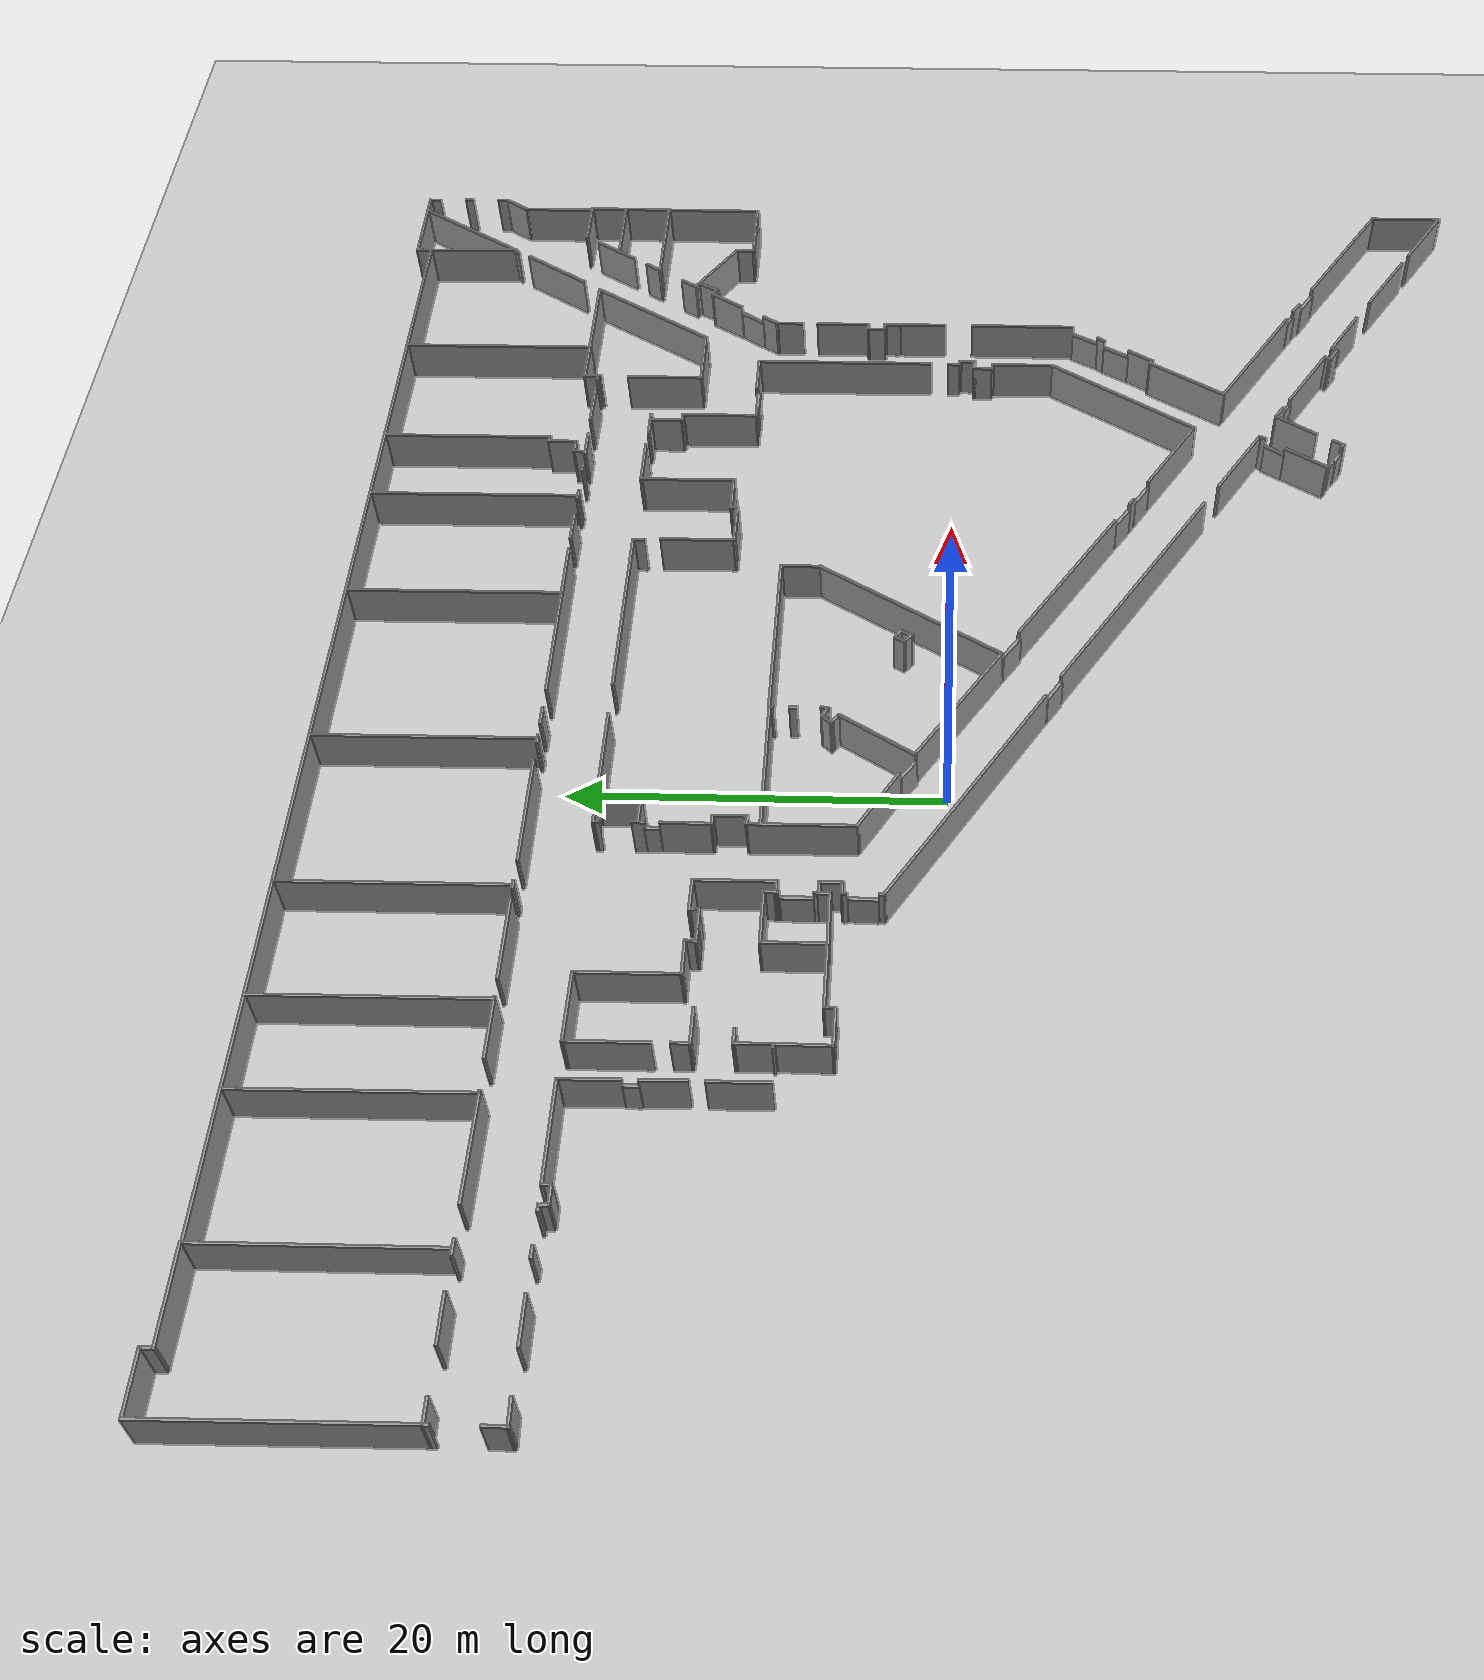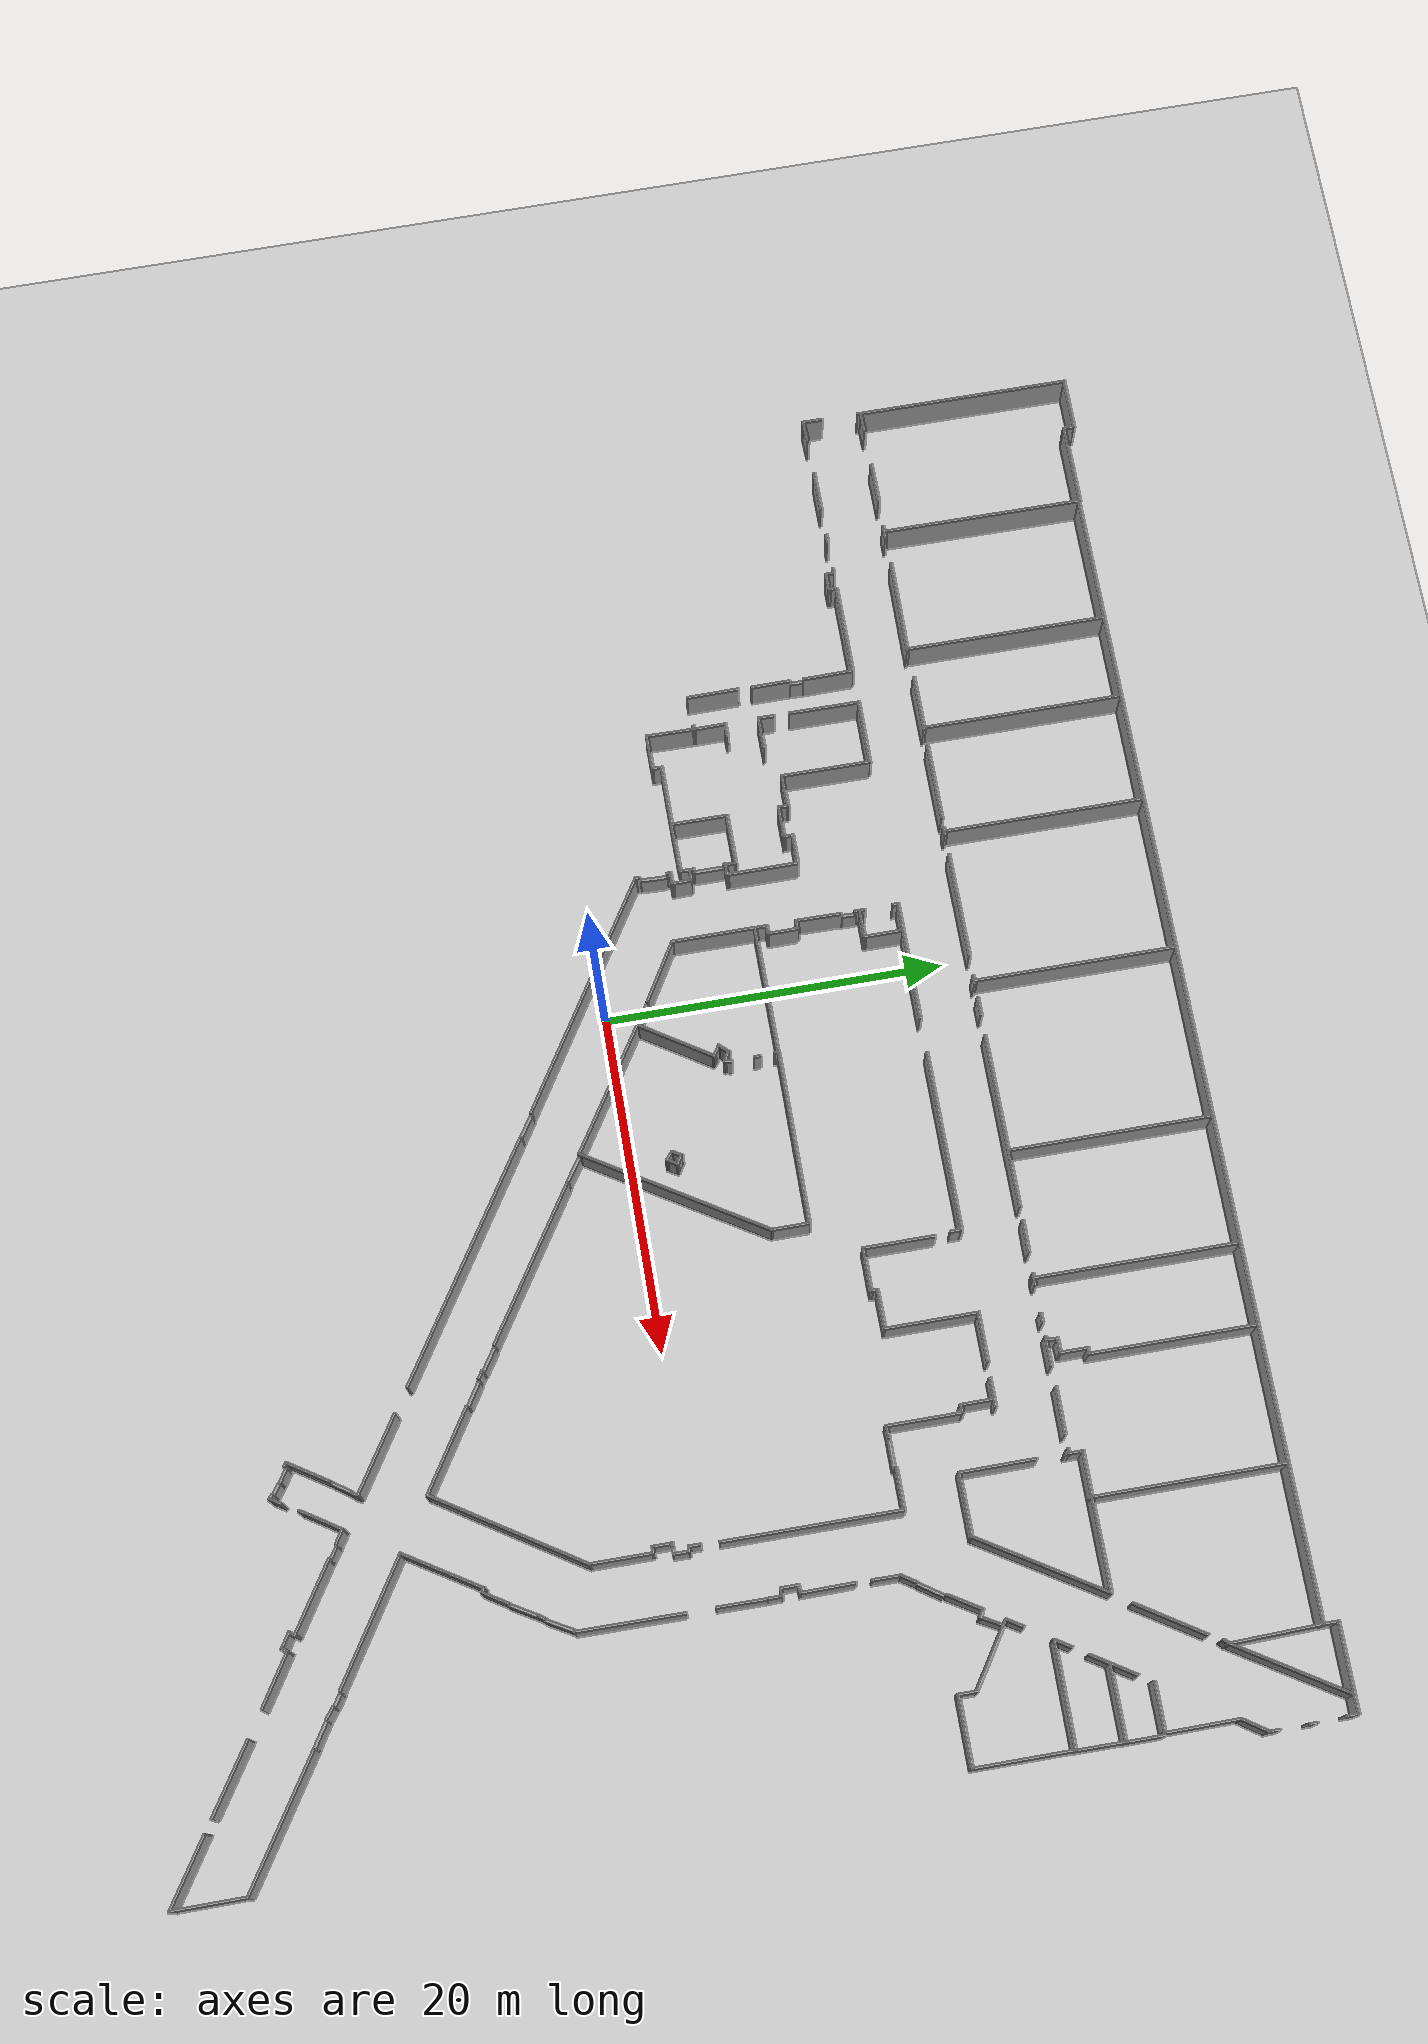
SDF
<sdf version="1.7">
 <world name="default">
  <light name="sun" type="directional">
   <pose>0 0 10 0 -0 0</pose>
   <diffuse>0.8 0.8 0.8 1</diffuse>
   <specular>0.2 0.2 0.2 1</specular>
   <attenuation>
    <range>1000</range>
    <constant>0.9</constant>
    <linear>0.01</linear>
    <quadratic>0.001</quadratic>
   </attenuation>
   <direction>-0.5 0.1 -0.9</direction>
   <spot><inner_angle>0</inner_angle><outer_angle>0</outer_angle><falloff>0</falloff></spot>
  </light>
  <model name="ground_plane">
   <static>1</static>
   <link name="link">
    <collision name="collision">
     <geometry><plane><normal>0 0 1</normal><size>100 100</size></plane></geometry>
     <surface><friction><ode><mu>100</mu><mu2>50</mu2></ode></friction></surface>
    </collision>
    <visual name="visual">
     <cast_shadows>0</cast_shadows>
     <geometry><plane><normal>0 0 1</normal><size>100 100</size></plane></geometry>
     <material>
      <script><uri>file://media/materials/scripts/gazebo.material</uri><name>Gazebo/Grey</name></script>
     </material>
    </visual>
   </link>
  </model>
  <gravity>0 0 -9.8</gravity>
  <magnetic_field>6e-06 2.3e-05 -4.2e-05</magnetic_field>
  <atmosphere type="adiabatic"/>
  <physics type="ode">
   <max_step_size>0.001</max_step_size>
   <real_time_factor>1</real_time_factor>
   <real_time_update_rate>1000</real_time_update_rate>
  </physics>
  <scene><ambient>0.4 0.4 0.4 1</ambient><background>0.7 0.7 0.7 1</background><shadows>1</shadows></scene>
  <spherical_coordinates>
   <surface_model>EARTH_WGS84</surface_model>
   <latitude_deg>0</latitude_deg>
   <longitude_deg>0</longitude_deg>
   <elevation>0</elevation>
   <heading_deg>0</heading_deg>
  </spherical_coordinates>
  <model name="Hopper_Basement">
   <pose>6.01939 1.54901 0 0 -0 0</pose>
   <link name="Door_1">
    <collision name="Door_1_Collision">
     <geometry><box><size>0.9 0.17 2</size></box></geometry>
     <pose>0 0 1 0 -0 0</pose>
    </collision>
    <visual name="Door_1_Visual">
     <pose>0 0 1 0 -0 0</pose>
     <geometry><box><size>0.9 0.17 2</size></box></geometry>
     <material>
      <script><uri>file://media/materials/scripts/gazebo.material</uri><name>Gazebo/Grey</name></script>
     </material>
    </visual>
    <pose>17.5368 -23.5338 0 0 -0 -0.56303</pose>
   </link>
   <link name="Door_10">
    <collision name="Door_10_Collision">
     <geometry><box><size>1.49816 0.2 2</size></box></geometry>
     <pose>0 0 1 0 -0 0</pose>
    </collision>
    <visual name="Door_10_Visual">
     <pose>0 0 1 0 -0 0</pose>
     <geometry><box><size>1.49816 0.2 2</size></box></geometry>
     <material>
      <script><uri>file://media/materials/scripts/gazebo.material</uri><name>Gazebo/Grey</name></script>
     </material>
    </visual>
    <pose>0.000581 -7.09301 0 0 -0 2.56816</pose>
   </link>
   <link name="Door_11">
    <collision name="Door_11_Collision">
     <geometry><box><size>1.38841 0.2 2</size></box></geometry>
     <pose>0 0 1 0 -0 0</pose>
    </collision>
    <visual name="Door_11_Visual">
     <pose>0 0 1 0 -0 0</pose>
     <geometry><box><size>1.38841 0.2 2</size></box></geometry>
     <material>
      <script><uri>file://media/materials/scripts/gazebo.material</uri><name>Gazebo/Grey</name></script>
     </material>
    </visual>
    <pose>-5.47167 0.553969 0 0 -0 2.53623</pose>
   </link>
   <link name="Door_12">
    <collision name="Door_12_Collision">
     <geometry><box><size>1.59688 0.2 2</size></box></geometry>
     <pose>0 0 1 0 -0 0</pose>
    </collision>
    <visual name="Door_12_Visual">
     <pose>0 0 1 0 -0 0</pose>
     <geometry><box><size>1.59688 0.2 2</size></box></geometry>
     <material>
      <script><uri>file://media/materials/scripts/gazebo.material</uri><name>Gazebo/Grey</name></script>
     </material>
    </visual>
    <pose>-13.5825 2.58994 0 0 -0 1.5371</pose>
   </link>
   <link name="Door_13">
    <collision name="Door_13_Collision">
     <geometry><box><size>1.81181 0.2 2</size></box></geometry>
     <pose>0 0 1 0 -0 0</pose>
    </collision>
    <visual name="Door_13_Visual">
     <pose>0 0 1 0 -0 0</pose>
     <geometry><box><size>1.81181 0.2 2</size></box></geometry>
     <material>
      <script><uri>file://media/materials/scripts/gazebo.material</uri><name>Gazebo/Grey</name></script>
     </material>
    </visual>
    <pose>-13.5678 5.87601 0 0 -0 1.5708</pose>
   </link>
   <link name="Door_14">
    <collision name="Door_14_Collision">
     <geometry><box><size>0.8396 0.2 2</size></box></geometry>
     <pose>0 0 1 0 -0 0</pose>
    </collision>
    <visual name="Door_14_Visual">
     <pose>0 0 1 0 -0 0</pose>
     <geometry><box><size>0.8396 0.2 2</size></box></geometry>
     <material>
      <script><uri>file://media/materials/scripts/gazebo.material</uri><name>Gazebo/Grey</name></script>
     </material>
    </visual>
    <pose>-9.41509 13.4537 0 0 -0 1.53451</pose>
   </link>
   <link name="Door_15">
    <collision name="Door_15_Collision">
     <geometry><box><size>0.817522 0.2 2</size></box></geometry>
     <pose>0 0 1 0 -0 0</pose>
    </collision>
    <visual name="Door_15_Visual">
     <pose>0 0 1 0 -0 0</pose>
     <geometry><box><size>0.817522 0.2 2</size></box></geometry>
     <material>
      <script><uri>file://media/materials/scripts/gazebo.material</uri><name>Gazebo/Grey</name></script>
     </material>
    </visual>
    <pose>-24.285 12.9691 0 0 -0 -1.59292</pose>
   </link>
   <link name="Door_16">
    <collision name="Door_16_Collision">
     <geometry><box><size>1.6484 0.2 2</size></box></geometry>
     <pose>0 0 1 0 -0 0</pose>
    </collision>
    <visual name="Door_16_Visual">
     <pose>0 0 1 0 -0 0</pose>
     <geometry><box><size>1.6484 0.2 2</size></box></geometry>
     <material>
      <script><uri>file://media/materials/scripts/gazebo.material</uri><name>Gazebo/Grey</name></script>
     </material>
    </visual>
    <pose>29.9742 10.9349 0 0 -0 0.972827</pose>
   </link>
   <link name="Door_17">
    <collision name="Door_17_Collision">
     <geometry><box><size>1.67833 0.2 2</size></box></geometry>
     <pose>0 0 1 0 -0 0</pose>
    </collision>
    <visual name="Door_17_Visual">
     <pose>0 0 1 0 -0 0</pose>
     <geometry><box><size>1.67833 0.2 2</size></box></geometry>
     <material>
      <script><uri>file://media/materials/scripts/gazebo.material</uri><name>Gazebo/Grey</name></script>
     </material>
    </visual>
    <pose>22.2042 10.1557 0 0 -0 0</pose>
   </link>
   <link name="Door_18">
    <collision name="Door_18_Collision">
     <geometry><box><size>1.69771 0.2 2</size></box></geometry>
     <pose>0 0 1 0 -0 0</pose>
    </collision>
    <visual name="Door_18_Visual">
     <pose>0 0 1 0 -0 0</pose>
     <geometry><box><size>1.69771 0.2 2</size></box></geometry>
     <material>
      <script><uri>file://media/materials/scripts/gazebo.material</uri><name>Gazebo/Grey</name></script>
     </material>
    </visual>
    <pose>27.2177 -11.4449 0 0 -0 1.03772</pose>
   </link>
   <link name="Door_19">
    <collision name="Door_19_Collision">
     <geometry><box><size>1.71307 0.2 2</size></box></geometry>
     <pose>0 0 1 0 -0 0</pose>
    </collision>
    <visual name="Door_19_Visual">
     <pose>0 0 1 0 -0 0</pose>
     <geometry><box><size>1.71307 0.2 2</size></box></geometry>
     <material>
      <script><uri>file://media/materials/scripts/gazebo.material</uri><name>Gazebo/Grey</name></script>
     </material>
    </visual>
    <pose>28.3872 -9.58453 0 0 -0 1.05525</pose>
   </link>
   <link name="Door_2">
    <collision name="Door_2_Collision">
     <geometry><box><size>0.767569 0.2 2</size></box></geometry>
     <pose>0 0 1 0 -0 0</pose>
    </collision>
    <visual name="Door_2_Visual">
     <pose>0 0 1 0 -0 0</pose>
     <geometry><box><size>0.767569 0.2 2</size></box></geometry>
     <material>
      <script><uri>file://media/materials/scripts/gazebo.material</uri><name>Gazebo/Grey</name></script>
     </material>
    </visual>
    <pose>18.2298 -24.0147 0 0 0 -0.60249</pose>
   </link>
   <link name="Door_3">
    <collision name="Door_3_Collision">
     <geometry><box><size>1.32468 0.2 2</size></box></geometry>
     <pose>0 0 1 0 -0 0</pose>
    </collision>
    <visual name="Door_3_Visual">
     <pose>0 0 1 0 -0 0</pose>
     <geometry><box><size>1.32468 0.2 2</size></box></geometry>
     <material>
      <script><uri>file://media/materials/scripts/gazebo.material</uri><name>Gazebo/Grey</name></script>
     </material>
    </visual>
    <pose>18.7678 -20.3905 0 0 0 -2.17722</pose>
   </link>
   <link name="Door_4">
    <collision name="Door_4_Collision">
     <geometry><box><size>0.9 0.17 2</size></box></geometry>
     <pose>0 0 1 0 -0 0</pose>
    </collision>
    <visual name="Door_4_Visual">
     <pose>0 0 1 0 -0 0</pose>
     <geometry><box><size>0.9 0.17 2</size></box></geometry>
     <material>
      <script><uri>file://media/materials/scripts/gazebo.material</uri><name>Gazebo/Grey</name></script>
     </material>
    </visual>
    <pose>22.2894 -21.3526 0 0 -0 2.55037</pose>
   </link>
   <link name="Door_5">
    <collision name="Door_5_Collision">
     <geometry><box><size>0.850621 0.2 2</size></box></geometry>
     <pose>0 0 1 0 -0 0</pose>
    </collision>
    <visual name="Door_5_Visual">
     <pose>0 0 1 0 -0 0</pose>
     <geometry><box><size>0.850621 0.2 2</size></box></geometry>
     <material>
      <script><uri>file://media/materials/scripts/gazebo.material</uri><name>Gazebo/Grey</name></script>
     </material>
    </visual>
    <pose>30.3252 -22.2534 0 0 0 -0.562767</pose>
   </link>
   <link name="Door_6">
    <collision name="Door_6_Collision">
     <geometry><box><size>1.59928 0.2 2</size></box></geometry>
     <pose>0 0 1 0 -0 0</pose>
    </collision>
    <visual name="Door_6_Visual">
     <pose>0 0 1 0 -0 0</pose>
     <geometry><box><size>1.59928 0.2 2</size></box></geometry>
     <material>
      <script><uri>file://media/materials/scripts/gazebo.material</uri><name>Gazebo/Grey</name></script>
     </material>
    </visual>
    <pose>31.9912 -23.4036 0 0 -0 2.58393</pose>
   </link>
   <link name="Door_7">
    <collision name="Door_7_Collision">
     <geometry><box><size>1.56615 0.2 2</size></box></geometry>
     <pose>0 0 1 0 -0 0</pose>
    </collision>
    <visual name="Door_7_Visual">
     <pose>0 0 1 0 -0 0</pose>
     <geometry><box><size>1.56615 0.2 2</size></box></geometry>
     <material>
      <script><uri>file://media/materials/scripts/gazebo.material</uri><name>Gazebo/Grey</name></script>
     </material>
    </visual>
    <pose>14.8119 -12.3698 0 0 -0 2.58025</pose>
   </link>
   <link name="Door_8">
    <collision name="Door_8_Collision">
     <geometry><box><size>1.56443 0.2 2</size></box></geometry>
     <pose>0 0 1 0 -0 0</pose>
    </collision>
    <visual name="Door_8_Visual">
     <pose>0 0 1 0 -0 0</pose>
     <geometry><box><size>1.56443 0.2 2</size></box></geometry>
     <material>
      <script><uri>file://media/materials/scripts/gazebo.material</uri><name>Gazebo/Grey</name></script>
     </material>
    </visual>
    <pose>13.0298 -11.2254 0 0 -0 2.55791</pose>
   </link>
   <link name="Door_9">
    <collision name="Door_9_Collision">
     <geometry><box><size>1.72128 0.2 2</size></box></geometry>
     <pose>0 0 1 0 -0 0</pose>
    </collision>
    <visual name="Door_9_Visual">
     <pose>0 0 1 0 -0 0</pose>
     <geometry><box><size>1.72128 0.2 2</size></box></geometry>
     <material>
      <script><uri>file://media/materials/scripts/gazebo.material</uri><name>Gazebo/Grey</name></script>
     </material>
    </visual>
    <pose>2.98021 -4.81191 0 0 -0 2.54196</pose>
   </link>
   <link name="Wall_10">
    <collision name="Wall_10_Collision">
     <geometry><box><size>4.03256 0.15 2.5</size></box></geometry>
     <pose>0 0 1.25 0 -0 0</pose>
    </collision>
    <visual name="Wall_10_Visual">
     <pose>0 0 1.25 0 -0 0</pose>
     <geometry><box><size>4.03256 0.15 2.5</size></box></geometry>
     <material>
      <script><uri>file://media/materials/scripts/gazebo.material</uri><name>Gazebo/Grey</name></script>
      <ambient>1 1 1 1</ambient>
     </material>
     <meta><layer>0</layer></meta>
    </visual>
    <pose>-7.77452 2.0023 0 0 -0 -0.539781</pose>
   </link>
   <link name="Wall_102">
    <collision name="Wall_102_Collision">
     <geometry><box><size>0.551094 0.15 2.5</size></box></geometry>
     <pose>0 0 1.25 0 -0 0</pose>
    </collision>
    <visual name="Wall_102_Visual">
     <pose>0 0 1.25 0 -0 0</pose>
     <geometry><box><size>0.551094 0.15 2.5</size></box></geometry>
     <material>
      <script><uri>file://media/materials/scripts/gazebo.material</uri><name>Gazebo/Grey</name></script>
      <ambient>1 1 1 1</ambient>
     </material>
     <meta><layer>0</layer></meta>
    </visual>
    <pose>-13.3988 19.8843 0 0 -0 0.021736</pose>
   </link>
   <link name="Wall_104">
    <collision name="Wall_104_Collision">
     <geometry><box><size>6.41785 0.15 2.5</size></box></geometry>
     <pose>0 0 1.25 0 -0 0</pose>
    </collision>
    <visual name="Wall_104_Visual">
     <pose>0 0 1.25 0 -0 0</pose>
     <geometry><box><size>6.41785 0.15 2.5</size></box></geometry>
     <material>
      <script><uri>file://media/materials/scripts/gazebo.material</uri><name>Gazebo/Grey</name></script>
      <ambient>1 1 1 1</ambient>
     </material>
     <meta><layer>0</layer></meta>
    </visual>
    <pose>-8.76549 19.8756 0 0 -0 0.004172</pose>
   </link>
   <link name="Wall_106">
    <collision name="Wall_106_Collision">
     <geometry><box><size>0.594672 0.15 2.5</size></box></geometry>
     <pose>0 0 1.25 0 -0 0</pose>
    </collision>
    <visual name="Wall_106_Visual">
     <pose>0 0 1.25 0 -0 0</pose>
     <geometry><box><size>0.594672 0.15 2.5</size></box></geometry>
     <material>
      <script><uri>file://media/materials/scripts/gazebo.material</uri><name>Gazebo/Grey</name></script>
      <ambient>1 1 1 1</ambient>
     </material>
     <meta><layer>0</layer></meta>
    </visual>
    <pose>-4.12784 19.8756 0 0 -0 -0.019605</pose>
   </link>
   <link name="Wall_108">
    <collision name="Wall_108_Collision">
     <geometry><box><size>1.14382 0.15 2.5</size></box></geometry>
     <pose>0 0 1.25 0 -0 0</pose>
    </collision>
    <visual name="Wall_108_Visual">
     <pose>0 0 1.25 0 -0 0</pose>
     <geometry><box><size>1.14382 0.15 2.5</size></box></geometry>
     <material>
      <script><uri>file://media/materials/scripts/gazebo.material</uri><name>Gazebo/Grey</name></script>
      <ambient>1 1 1 1</ambient>
     </material>
     <meta><layer>0</layer></meta>
    </visual>
    <pose>-2.51949 19.8799 0 0 -0 0</pose>
   </link>
   <link name="Wall_111">
    <collision name="Wall_111_Collision">
     <geometry><box><size>10.4156 0.15 2.5</size></box></geometry>
     <pose>0 0 1.25 0 -0 0</pose>
    </collision>
    <visual name="Wall_111_Visual">
     <pose>0 0 1.25 0 -0 0</pose>
     <geometry><box><size>10.4156 0.15 2.5</size></box></geometry>
     <material>
      <script><uri>file://media/materials/scripts/gazebo.material</uri><name>Gazebo/Grey</name></script>
      <ambient>1 1 1 1</ambient>
     </material>
     <meta><layer>0</layer></meta>
    </visual>
    <pose>4.43559 19.8813 0 0 -0 0.00293</pose>
   </link>
   <link name="Wall_113">
    <collision name="Wall_113_Collision">
     <geometry><box><size>1.97466 0.15 2.5</size></box></geometry>
     <pose>0 0 1.25 0 -0 0</pose>
    </collision>
    <visual name="Wall_113_Visual">
     <pose>0 0 1.25 0 -0 0</pose>
     <geometry><box><size>1.97466 0.15 2.5</size></box></geometry>
     <material>
      <script><uri>file://media/materials/scripts/gazebo.material</uri><name>Gazebo/Grey</name></script>
      <ambient>1 1 1 1</ambient>
     </material>
     <meta><layer>0</layer></meta>
    </visual>
    <pose>11.3328 19.8964 0 0 -0 -0.010989</pose>
   </link>
   <link name="Wall_115">
    <collision name="Wall_115_Collision">
     <geometry><box><size>0.781654 0.15 2.5</size></box></geometry>
     <pose>0 0 1.25 0 -0 0</pose>
    </collision>
    <visual name="Wall_115_Visual">
     <pose>0 0 1.25 0 -0 0</pose>
     <geometry><box><size>0.781654 0.15 2.5</size></box></geometry>
     <material>
      <script><uri>file://media/materials/scripts/gazebo.material</uri><name>Gazebo/Grey</name></script>
      <ambient>1 1 1 1</ambient>
     </material>
     <meta><layer>0</layer></meta>
    </visual>
    <pose>13.8541 19.8813 0 0 -0 -0.015872</pose>
   </link>
   <link name="Wall_117">
    <collision name="Wall_117_Collision">
     <geometry><box><size>0.621174 0.15 2.5</size></box></geometry>
     <pose>0 0 1.25 0 -0 0</pose>
    </collision>
    <visual name="Wall_117_Visual">
     <pose>0 0 1.25 0 -0 0</pose>
     <geometry><box><size>0.621174 0.15 2.5</size></box></geometry>
     <material>
      <script><uri>file://media/materials/scripts/gazebo.material</uri><name>Gazebo/Grey</name></script>
      <ambient>1 1 1 1</ambient>
     </material>
     <meta><layer>0</layer></meta>
    </visual>
    <pose>16.0896 19.8713 0 0 -0 0.021273</pose>
   </link>
   <link name="Wall_119">
    <collision name="Wall_119_Collision">
     <geometry><box><size>1.7941 0.15 2.5</size></box></geometry>
     <pose>0 0 1.25 0 -0 0</pose>
    </collision>
    <visual name="Wall_119_Visual">
     <pose>0 0 1.25 0 -0 0</pose>
     <geometry><box><size>1.7941 0.15 2.5</size></box></geometry>
     <material>
      <script><uri>file://media/materials/scripts/gazebo.material</uri><name>Gazebo/Grey</name></script>
      <ambient>1 1 1 1</ambient>
     </material>
     <meta><layer>0</layer></meta>
    </visual>
    <pose>18.0495 19.8763 0 0 -0 0</pose>
   </link>
   <link name="Wall_12">
    <collision name="Wall_12_Collision">
     <geometry><box><size>0.50762 0.15 2.5</size></box></geometry>
     <pose>0 0 1.25 0 -0 0</pose>
    </collision>
    <visual name="Wall_12_Visual">
     <pose>0 0 1.25 0 -0 0</pose>
     <geometry><box><size>0.50762 0.15 2.5</size></box></geometry>
     <material>
      <script><uri>file://media/materials/scripts/gazebo.material</uri><name>Gazebo/Grey</name></script>
      <ambient>1 1 1 1</ambient>
     </material>
     <meta><layer>0</layer></meta>
    </visual>
    <pose>-1.74517 4.99309 0 0 -0 -1.76819</pose>
   </link>
   <link name="Wall_121">
    <collision name="Wall_121_Collision">
     <geometry><box><size>2.81672 0.15 2.5</size></box></geometry>
     <pose>0 0 1.25 0 -0 0</pose>
    </collision>
    <visual name="Wall_121_Visual">
     <pose>0 0 1.25 0 -0 0</pose>
     <geometry><box><size>2.81672 0.15 2.5</size></box></geometry>
     <material>
      <script><uri>file://media/materials/scripts/gazebo.material</uri><name>Gazebo/Grey</name></script>
      <ambient>1 1 1 1</ambient>
     </material>
     <meta><layer>0</layer></meta>
    </visual>
    <pose>21.458 19.8863 0 0 -0 -0.007519</pose>
   </link>
   <link name="Wall_123">
    <collision name="Wall_123_Collision">
     <geometry><box><size>0.3906 0.15 2.5</size></box></geometry>
     <pose>0 0 1.25 0 -0 0</pose>
    </collision>
    <visual name="Wall_123_Visual">
     <pose>0 0 1.25 0 -0 0</pose>
     <geometry><box><size>0.3906 0.15 2.5</size></box></geometry>
     <material>
      <script><uri>file://media/materials/scripts/gazebo.material</uri><name>Gazebo/Grey</name></script>
      <ambient>1 1 1 1</ambient>
     </material>
     <meta><layer>0</layer></meta>
    </visual>
    <pose>23.7838 19.8863 0 0 -0 0</pose>
   </link>
   <link name="Wall_124">
    <collision name="Wall_124_Collision">
     <geometry><box><size>0.3104 0.15 2.5</size></box></geometry>
     <pose>0 0 1.25 0 -0 0</pose>
    </collision>
    <visual name="Wall_124_Visual">
     <pose>0 0 1.25 0 -0 0</pose>
     <geometry><box><size>0.3104 0.15 2.5</size></box></geometry>
     <material>
      <script><uri>file://media/materials/scripts/gazebo.material</uri><name>Gazebo/Grey</name></script>
      <ambient>1 1 1 1</ambient>
     </material>
     <meta><layer>0</layer></meta>
    </visual>
    <pose>23.9091 19.8061 0 0 -0 -1.50838</pose>
   </link>
   <link name="Wall_126">
    <collision name="Wall_126_Collision">
     <geometry><box><size>4.50086 0.15 2.5</size></box></geometry>
     <pose>0 0 1.25 0 -0 0</pose>
    </collision>
    <visual name="Wall_126_Visual">
     <pose>0 0 1.25 0 -0 0</pose>
     <geometry><box><size>4.50086 0.15 2.5</size></box></geometry>
     <material>
      <script><uri>file://media/materials/scripts/gazebo.material</uri><name>Gazebo/Grey</name></script>
      <ambient>1 1 1 1</ambient>
     </material>
     <meta><layer>0</layer></meta>
    </visual>
    <pose>23.8941 15.8363 0 0 -0 -1.56619</pose>
   </link>
   <link name="Wall_127">
    <collision name="Wall_127_Collision">
     <geometry><box><size>3.77906 0.15 2.5</size></box></geometry>
     <pose>0 0 1.25 0 -0 0</pose>
    </collision>
    <visual name="Wall_127_Visual">
     <pose>0 0 1.25 0 -0 0</pose>
     <geometry><box><size>3.77906 0.15 2.5</size></box></geometry>
     <material>
      <script><uri>file://media/materials/scripts/gazebo.material</uri><name>Gazebo/Grey</name></script>
      <ambient>1 1 1 1</ambient>
     </material>
     <meta><layer>0</layer></meta>
    </visual>
    <pose>25.7186 13.6658 0 0 -0 0.002762</pose>
   </link>
   <link name="Wall_129">
    <collision name="Wall_129_Collision">
     <geometry><box><size>1.13114 0.15 2.5</size></box></geometry>
     <pose>0 0 1.25 0 -0 0</pose>
    </collision>
    <visual name="Wall_129_Visual">
     <pose>0 0 1.25 0 -0 0</pose>
     <geometry><box><size>1.13114 0.15 2.5</size></box></geometry>
     <material>
      <script><uri>file://media/materials/scripts/gazebo.material</uri><name>Gazebo/Grey</name></script>
      <ambient>1 1 1 1</ambient>
     </material>
     <meta><layer>0</layer></meta>
    </visual>
    <pose>29.2187 9.80355 0 0 -0 -2.14587</pose>
   </link>
   <link name="Wall_13">
    <collision name="Wall_13_Collision">
     <geometry><box><size>0.75 0.15 2.5</size></box></geometry>
     <pose>0 0 1.25 0 -0 0</pose>
    </collision>
    <visual name="Wall_13_Visual">
     <pose>0 0 1.25 0 -0 0</pose>
     <geometry><box><size>0.75 0.15 2.5</size></box></geometry>
     <material>
      <script><uri>file://media/materials/scripts/gazebo.material</uri><name>Gazebo/Grey</name></script>
      <ambient>1 1 1 1</ambient>
     </material>
     <meta><layer>0</layer></meta>
    </visual>
    <pose>-2.04005 4.96775 0 0 -0 2.61799</pose>
   </link>
   <link name="Wall_130">
    <collision name="Wall_130_Collision">
     <geometry><box><size>1.70584 0.15 2.5</size></box></geometry>
     <pose>0 0 1.25 0 -0 0</pose>
    </collision>
    <visual name="Wall_130_Visual">
     <pose>0 0 1.25 0 -0 0</pose>
     <geometry><box><size>1.70584 0.15 2.5</size></box></geometry>
     <material>
      <script><uri>file://media/materials/scripts/gazebo.material</uri><name>Gazebo/Grey</name></script>
      <ambient>1 1 1 1</ambient>
     </material>
     <meta><layer>0</layer></meta>
    </visual>
    <pose>28.9443 8.61431 0 0 -0 -1.5806</pose>
   </link>
   <link name="Wall_133">
    <collision name="Wall_133_Collision">
     <geometry><box><size>3.22589 0.15 2.5</size></box></geometry>
     <pose>0 0 1.25 0 -0 0</pose>
    </collision>
    <visual name="Wall_133_Visual">
     <pose>0 0 1.25 0 -0 0</pose>
     <geometry><box><size>3.22589 0.15 2.5</size></box></geometry>
     <material>
      <script><uri>file://media/materials/scripts/gazebo.material</uri><name>Gazebo/Grey</name></script>
      <ambient>1 1 1 1</ambient>
     </material>
     <meta><layer>0</layer></meta>
    </visual>
    <pose>28.9359 5.31794 0 0 -0 -1.56218</pose>
   </link>
   <link name="Wall_134">
    <collision name="Wall_134_Collision">
     <geometry><box><size>0.602525 0.15 2.5</size></box></geometry>
     <pose>0 0 1.25 0 -0 0</pose>
    </collision>
    <visual name="Wall_134_Visual">
     <pose>0 0 1.25 0 -0 0</pose>
     <geometry><box><size>0.602525 0.15 2.5</size></box></geometry>
     <material>
      <script><uri>file://media/materials/scripts/gazebo.material</uri><name>Gazebo/Grey</name></script>
      <ambient>1 1 1 1</ambient>
     </material>
     <meta><layer>0</layer></meta>
    </visual>
    <pose>28.7238 3.76012 0 0 -0 -3.05358</pose>
   </link>
   <link name="Wall_135">
    <collision name="Wall_135_Collision">
     <geometry><box><size>1.13119 0.15 2.5</size></box></geometry>
     <pose>0 0 1.25 0 -0 0</pose>
    </collision>
    <visual name="Wall_135_Visual">
     <pose>0 0 1.25 0 -0 0</pose>
     <geometry><box><size>1.13119 0.15 2.5</size></box></geometry>
     <material>
      <script><uri>file://media/materials/scripts/gazebo.material</uri><name>Gazebo/Grey</name></script>
      <ambient>1 1 1 1</ambient>
     </material>
     <meta><layer>0</layer></meta>
    </visual>
    <pose>28.505 3.24968 0 0 -0 -1.55728</pose>
   </link>
   <link name="Wall_136">
    <collision name="Wall_136_Collision">
     <geometry><box><size>0.587716 0.15 2.5</size></box></geometry>
     <pose>0 0 1.25 0 -0 0</pose>
    </collision>
    <visual name="Wall_136_Visual">
     <pose>0 0 1.25 0 -0 0</pose>
     <geometry><box><size>0.587716 0.15 2.5</size></box></geometry>
     <material>
      <script><uri>file://media/materials/scripts/gazebo.material</uri><name>Gazebo/Grey</name></script>
      <ambient>1 1 1 1</ambient>
     </material>
     <meta><layer>0</layer></meta>
    </visual>
    <pose>28.7304 2.75251 0 0 -0 -0.030294</pose>
   </link>
   <link name="Wall_137">
    <collision name="Wall_137_Collision">
     <geometry><box><size>1 0.15 2.5</size></box></geometry>
     <pose>0 0 1.25 0 -0 0</pose>
    </collision>
    <visual name="Wall_137_Visual">
     <pose>0 0 1.25 0 -0 0</pose>
     <geometry><box><size>1 0.15 2.5</size></box></geometry>
     <material>
      <script><uri>file://media/materials/scripts/gazebo.material</uri><name>Gazebo/Grey</name></script>
      <ambient>1 1 1 1</ambient>
     </material>
     <meta><layer>0</layer></meta>
    </visual>
    <pose>28.9491 2.32088 0 0 -0 -1.5708</pose>
   </link>
   <link name="Wall_139">
    <collision name="Wall_139_Collision">
     <geometry><box><size>2.88119 0.15 2.5</size></box></geometry>
     <pose>0 0 1.25 0 -0 0</pose>
    </collision>
    <visual name="Wall_139_Visual">
     <pose>0 0 1.25 0 -0 0</pose>
     <geometry><box><size>2.88119 0.15 2.5</size></box></geometry>
     <material>
      <script><uri>file://media/materials/scripts/gazebo.material</uri><name>Gazebo/Grey</name></script>
      <ambient>1 1 1 1</ambient>
     </material>
     <meta><layer>0</layer></meta>
    </visual>
    <pose>28.9491 0.465496 0 0 -0 1.56109</pose>
   </link>
   <link name="Wall_14">
    <collision name="Wall_14_Collision">
     <geometry><box><size>0.838631 0.15 2.5</size></box></geometry>
     <pose>0 0 1.25 0 -0 0</pose>
    </collision>
    <visual name="Wall_14_Visual">
     <pose>0 0 1.25 0 -0 0</pose>
     <geometry><box><size>0.838631 0.15 2.5</size></box></geometry>
     <material>
      <script><uri>file://media/materials/scripts/gazebo.material</uri><name>Gazebo/Grey</name></script>
      <ambient>1 1 1 1</ambient>
     </material>
     <meta><layer>0</layer></meta>
    </visual>
    <pose>-2.53099 4.86255 0 0 -0 -2.30675</pose>
   </link>
   <link name="Wall_141">
    <collision name="Wall_141_Collision">
     <geometry><box><size>6.28034 0.15 2.5</size></box></geometry>
     <pose>0 0 1.25 0 -0 0</pose>
    </collision>
    <visual name="Wall_141_Visual">
     <pose>0 0 1.25 0 -0 0</pose>
     <geometry><box><size>6.28034 0.15 2.5</size></box></geometry>
     <material>
      <script><uri>file://media/materials/scripts/gazebo.material</uri><name>Gazebo/Grey</name></script>
      <ambient>1 1 1 1</ambient>
     </material>
     <meta><layer>0</layer></meta>
    </visual>
    <pose>28.9323 -5.7266 0 0 -0 -1.57737</pose>
   </link>
   <link name="Wall_144">
    <collision name="Wall_144_Collision">
     <geometry><box><size>0.525069 0.15 2.5</size></box></geometry>
     <pose>0 0 1.25 0 -0 0</pose>
    </collision>
    <visual name="Wall_144_Visual">
     <pose>0 0 1.25 0 -0 0</pose>
     <geometry><box><size>0.525069 0.15 2.5</size></box></geometry>
     <material>
      <script><uri>file://media/materials/scripts/gazebo.material</uri><name>Gazebo/Grey</name></script>
      <ambient>1 1 1 1</ambient>
     </material>
     <meta><layer>0</layer></meta>
    </visual>
    <pose>27.8132 -10.4953 0 0 -0 -2.20355</pose>
   </link>
   <link name="Wall_146">
    <collision name="Wall_146_Collision">
     <geometry><box><size>1.71931 0.15 2.5</size></box></geometry>
     <pose>0 0 1.25 0 -0 0</pose>
    </collision>
    <visual name="Wall_146_Visual">
     <pose>0 0 1.25 0 -0 0</pose>
     <geometry><box><size>1.71931 0.15 2.5</size></box></geometry>
     <material>
      <script><uri>file://media/materials/scripts/gazebo.material</uri><name>Gazebo/Grey</name></script>
      <ambient>1 1 1 1</ambient>
     </material>
     <meta><layer>0</layer></meta>
    </visual>
    <pose>26.3457 -12.8341 0 0 -0 -2.13455</pose>
   </link>
   <link name="Wall_147">
    <collision name="Wall_147_Collision">
     <geometry><box><size>0.410537 0.15 2.5</size></box></geometry>
     <pose>0 0 1.25 0 -0 0</pose>
    </collision>
    <visual name="Wall_147_Visual">
     <pose>0 0 1.25 0 -0 0</pose>
     <geometry><box><size>0.410537 0.15 2.5</size></box></geometry>
     <material>
      <script><uri>file://media/materials/scripts/gazebo.material</uri><name>Gazebo/Grey</name></script>
      <ambient>1 1 1 1</ambient>
     </material>
     <meta><layer>0</layer></meta>
    </visual>
    <pose>25.8044 -13.4516 0 0 -0 2.78282</pose>
   </link>
   <link name="Wall_148">
    <collision name="Wall_148_Collision">
     <geometry><box><size>5.17139 0.15 2.5</size></box></geometry>
     <pose>0 0 1.25 0 -0 0</pose>
    </collision>
    <visual name="Wall_148_Visual">
     <pose>0 0 1.25 0 -0 0</pose>
     <geometry><box><size>5.17139 0.15 2.5</size></box></geometry>
     <material>
      <script><uri>file://media/materials/scripts/gazebo.material</uri><name>Gazebo/Grey</name></script>
      <ambient>1 1 1 1</ambient>
     </material>
     <meta><layer>0</layer></meta>
    </visual>
    <pose>24.3483 -15.5328 0 0 -0 -2.13101</pose>
   </link>
   <link name="Wall_15">
    <collision name="Wall_15_Collision">
     <geometry><box><size>0.811653 0.15 2.5</size></box></geometry>
     <pose>0 0 1.25 0 -0 0</pose>
    </collision>
    <visual name="Wall_15_Visual">
     <pose>0 0 1.25 0 -0 0</pose>
     <geometry><box><size>0.811653 0.15 2.5</size></box></geometry>
     <material>
      <script><uri>file://media/materials/scripts/gazebo.material</uri><name>Gazebo/Grey</name></script>
      <ambient>1 1 1 1</ambient>
     </material>
     <meta><layer>0</layer></meta>
    </visual>
    <pose>-2.48159 4.43201 0 0 -0 -0.558599</pose>
   </link>
   <link name="Wall_150">
    <collision name="Wall_150_Collision">
     <geometry><box><size>8.26316 0.15 2.5</size></box></geometry>
     <pose>0 0 1.25 0 -0 0</pose>
    </collision>
    <visual name="Wall_150_Visual">
     <pose>0 0 1.25 0 -0 0</pose>
     <geometry><box><size>8.26316 0.15 2.5</size></box></geometry>
     <material>
      <script><uri>file://media/materials/scripts/gazebo.material</uri><name>Gazebo/Grey</name></script>
      <ambient>1 1 1 1</ambient>
     </material>
     <meta><layer>0</layer></meta>
    </visual>
    <pose>26.4448 -19.8248 0 0 -0 -0.562982</pose>
   </link>
   <link name="Wall_152">
    <collision name="Wall_152_Collision">
     <geometry><box><size>0.890998 0.15 2.5</size></box></geometry>
     <pose>0 0 1.25 0 -0 0</pose>
    </collision>
    <visual name="Wall_152_Visual">
     <pose>0 0 1.25 0 -0 0</pose>
     <geometry><box><size>0.890998 0.15 2.5</size></box></geometry>
     <material>
      <script><uri>file://media/materials/scripts/gazebo.material</uri><name>Gazebo/Grey</name></script>
      <ambient>1 1 1 1</ambient>
     </material>
     <meta><layer>0</layer></meta>
    </visual>
    <pose>30.9654 -22.6988 0 0 -0 -0.639386</pose>
   </link>
   <link name="Wall_154">
    <collision name="Wall_154_Collision">
     <geometry><box><size>2.81857 0.15 2.5</size></box></geometry>
     <pose>0 0 1.25 0 -0 0</pose>
    </collision>
    <visual name="Wall_154_Visual">
     <pose>0 0 1.25 0 -0 0</pose>
     <geometry><box><size>2.81857 0.15 2.5</size></box></geometry>
     <material>
      <script><uri>file://media/materials/scripts/gazebo.material</uri><name>Gazebo/Grey</name></script>
      <ambient>1 1 1 1</ambient>
     </material>
     <meta><layer>0</layer></meta>
    </visual>
    <pose>17.655 -22.0889 0 0 -0 -2.14454</pose>
   </link>
   <link name="Wall_155">
    <collision name="Wall_155_Collision">
     <geometry><box><size>0.33611 0.15 2.5</size></box></geometry>
     <pose>0 0 1.25 0 -0 0</pose>
    </collision>
    <visual name="Wall_155_Visual">
     <pose>0 0 1.25 0 -0 0</pose>
     <geometry><box><size>0.33611 0.15 2.5</size></box></geometry>
     <material>
      <script><uri>file://media/materials/scripts/gazebo.material</uri><name>Gazebo/Grey</name></script>
      <ambient>1 1 1 1</ambient>
     </material>
     <meta><layer>0</layer></meta>
    </visual>
    <pose>17.007 -23.2629 0 0 -0 -0.610726</pose>
   </link>
   <link name="Wall_157">
    <collision name="Wall_157_Collision">
     <geometry><box><size>0.388162 0.15 2.5</size></box></geometry>
     <pose>0 0 1.25 0 -0 0</pose>
    </collision>
    <visual name="Wall_157_Visual">
     <pose>0 0 1.25 0 -0 0</pose>
     <geometry><box><size>0.388162 0.15 2.5</size></box></geometry>
     <material>
      <script><uri>file://media/materials/scripts/gazebo.material</uri><name>Gazebo/Grey</name></script>
      <ambient>1 1 1 1</ambient>
     </material>
     <meta><layer>0</layer></meta>
    </visual>
    <pose>18.6842 -24.3073 0 0 -0 -0.694738</pose>
   </link>
   <link name="Wall_158">
    <collision name="Wall_158_Collision">
     <geometry><box><size>0.835256 0.15 2.5</size></box></geometry>
     <pose>0 0 1.25 0 -0 0</pose>
    </collision>
    <visual name="Wall_158_Visual">
     <pose>0 0 1.25 0 -0 0</pose>
     <geometry><box><size>0.835256 0.15 2.5</size></box></geometry>
     <material>
      <script><uri>file://media/materials/scripts/gazebo.material</uri><name>Gazebo/Grey</name></script>
      <ambient>1 1 1 1</ambient>
     </material>
     <meta><layer>0</layer></meta>
    </visual>
    <pose>18.9586 -24.0938 0 0 -0 1.00748</pose>
   </link>
   <link name="Wall_16">
    <collision name="Wall_16_Collision">
     <geometry><box><size>4.97507 0.15 2.5</size></box></geometry>
     <pose>0 0 1.25 0 -0 0</pose>
    </collision>
    <visual name="Wall_16_Visual">
     <pose>0 0 1.25 0 -0 0</pose>
     <geometry><box><size>4.97507 0.15 2.5</size></box></geometry>
     <material>
      <script><uri>file://media/materials/scripts/gazebo.material</uri><name>Gazebo/Grey</name></script>
      <ambient>1 1 1 1</ambient>
     </material>
     <meta><layer>0</layer></meta>
    </visual>
    <pose>-3.49855 2.22275 0 0 -0 -2.13864</pose>
   </link>
   <link name="Wall_160">
    <collision name="Wall_160_Collision">
     <geometry><box><size>2.78469 0.15 2.5</size></box></geometry>
     <pose>0 0 1.25 0 -0 0</pose>
    </collision>
    <visual name="Wall_160_Visual">
     <pose>0 0 1.25 0 -0 0</pose>
     <geometry><box><size>2.78469 0.15 2.5</size></box></geometry>
     <material>
      <script><uri>file://media/materials/scripts/gazebo.material</uri><name>Gazebo/Grey</name></script>
      <ambient>1 1 1 1</ambient>
     </material>
     <meta><layer>0</layer></meta>
    </visual>
    <pose>20.4223 -21.7382 0 0 -0 0.995634</pose>
   </link>
   <link name="Wall_161">
    <collision name="Wall_161_Collision">
     <geometry><box><size>1.01303 0.15 2.5</size></box></geometry>
     <pose>0 0 1.25 0 -0 0</pose>
    </collision>
    <visual name="Wall_161_Visual">
     <pose>0 0 1.25 0 -0 0</pose>
     <geometry><box><size>1.01303 0.15 2.5</size></box></geometry>
     <material>
      <script><uri>file://media/materials/scripts/gazebo.material</uri><name>Gazebo/Grey</name></script>
      <ambient>1 1 1 1</ambient>
     </material>
     <meta><layer>0</layer></meta>
    </visual>
    <pose>21.5048 -20.8615 0 0 -0 -0.558599</pose>
   </link>
   <link name="Wall_163">
    <collision name="Wall_163_Collision">
     <geometry><box><size>4.68016 0.15 2.5</size></box></geometry>
     <pose>0 0 1.25 0 -0 0</pose>
    </collision>
    <visual name="Wall_163_Visual">
     <pose>0 0 1.25 0 -0 0</pose>
     <geometry><box><size>4.68016 0.15 2.5</size></box></geometry>
     <material>
      <script><uri>file://media/materials/scripts/gazebo.material</uri><name>Gazebo/Grey</name></script>
      <ambient>1 1 1 1</ambient>
     </material>
     <meta><layer>0</layer></meta>
    </visual>
    <pose>24.5465 -22.8055 0 0 -0 -0.564664</pose>
   </link>
   <link name="Wall_164">
    <collision name="Wall_164_Collision">
     <geometry><box><size>0.509836 0.15 2.5</size></box></geometry>
     <pose>0 0 1.25 0 -0 0</pose>
    </collision>
    <visual name="Wall_164_Visual">
     <pose>0 0 1.25 0 -0 0</pose>
     <geometry><box><size>0.509836 0.15 2.5</size></box></geometry>
     <material>
      <script><uri>file://media/materials/scripts/gazebo.material</uri><name>Gazebo/Grey</name></script>
      <ambient>1 1 1 1</ambient>
     </material>
     <meta><layer>0</layer></meta>
    </visual>
    <pose>26.3533 -24.1625 0 0 -0 -2.20582</pose>
   </link>
   <link name="Wall_165">
    <collision name="Wall_165_Collision">
     <geometry><box><size>1.10191 0.15 2.5</size></box></geometry>
     <pose>0 0 1.25 0 -0 0</pose>
    </collision>
    <visual name="Wall_165_Visual">
     <pose>0 0 1.25 0 -0 0</pose>
     <geometry><box><size>1.10191 0.15 2.5</size></box></geometry>
     <material>
      <script><uri>file://media/materials/scripts/gazebo.material</uri><name>Gazebo/Grey</name></script>
      <ambient>1 1 1 1</ambient>
     </material>
     <meta><layer>0</layer></meta>
    </visual>
    <pose>26.6506 -24.5589 0 0 -0 -0.556902</pose>
   </link>
   <link name="Wall_166">
    <collision name="Wall_166_Collision">
     <geometry><box><size>0.497679 0.15 2.5</size></box></geometry>
     <pose>0 0 1.25 0 -0 0</pose>
    </collision>
    <visual name="Wall_166_Visual">
     <pose>0 0 1.25 0 -0 0</pose>
     <geometry><box><size>0.497679 0.15 2.5</size></box></geometry>
     <material>
      <script><uri>file://media/materials/scripts/gazebo.material</uri><name>Gazebo/Grey</name></script>
      <ambient>1 1 1 1</ambient>
     </material>
     <meta><layer>0</layer></meta>
    </visual>
    <pose>27.1614 -24.6732 0 0 -0 0.909753</pose>
   </link>
   <link name="Wall_168">
    <collision name="Wall_168_Collision">
     <geometry><box><size>3.5003 0.15 2.5</size></box></geometry>
     <pose>0 0 1.25 0 -0 0</pose>
    </collision>
    <visual name="Wall_168_Visual">
     <pose>0 0 1.25 0 -0 0</pose>
     <geometry><box><size>3.5003 0.15 2.5</size></box></geometry>
     <material>
      <script><uri>file://media/materials/scripts/gazebo.material</uri><name>Gazebo/Grey</name></script>
      <ambient>1 1 1 1</ambient>
     </material>
     <meta><layer>0</layer></meta>
    </visual>
    <pose>28.686 -25.4279 0 0 -0 -0.561494</pose>
   </link>
   <link name="Wall_17">
    <collision name="Wall_17_Collision">
     <geometry><box><size>8.49585 0.15 2.5</size></box></geometry>
     <pose>0 0 1.25 0 -0 0</pose>
    </collision>
    <visual name="Wall_17_Visual">
     <pose>0 0 1.25 0 -0 0</pose>
     <geometry><box><size>8.49585 0.15 2.5</size></box></geometry>
     <material>
      <script><uri>file://media/materials/scripts/gazebo.material</uri><name>Gazebo/Grey</name></script>
      <ambient>1 1 1 1</ambient>
     </material>
     <meta><layer>0</layer></meta>
    </visual>
    <pose>-1.2893 -2.07302 0 0 -0 -0.572852</pose>
   </link>
   <link name="Wall_170">
    <collision name="Wall_170_Collision">
     <geometry><box><size>8.6046 0.15 2.5</size></box></geometry>
     <pose>0 0 1.25 0 -0 0</pose>
    </collision>
    <visual name="Wall_170_Visual">
     <pose>0 0 1.25 0 -0 0</pose>
     <geometry><box><size>8.6046 0.15 2.5</size></box></geometry>
     <material>
      <script><uri>file://media/materials/scripts/gazebo.material</uri><name>Gazebo/Grey</name></script>
      <ambient>1 1 1 1</ambient>
     </material>
     <meta><layer>0</layer></meta>
    </visual>
    <pose>36.3323 -26.114 0 0 -0 -0.569495</pose>
   </link>
   <link name="Wall_173">
    <collision name="Wall_173_Collision">
     <geometry><box><size>4.68372 0.15 2.5</size></box></geometry>
     <pose>0 0 1.25 0 -0 0</pose>
    </collision>
    <visual name="Wall_173_Visual">
     <pose>0 0 1.25 0 -0 0</pose>
     <geometry><box><size>4.68372 0.15 2.5</size></box></geometry>
     <material>
      <script><uri>file://media/materials/scripts/gazebo.material</uri><name>Gazebo/Grey</name></script>
      <ambient>1 1 1 1</ambient>
     </material>
     <meta><layer>0</layer></meta>
    </visual>
    <pose>33.5345 -28.5383 0 0 -0 -0.572146</pose>
   </link>
   <link name="Wall_175">
    <collision name="Wall_175_Collision">
     <geometry><box><size>4.49776 0.15 2.5</size></box></geometry>
     <pose>0 0 1.25 0 -0 0</pose>
    </collision>
    <visual name="Wall_175_Visual">
     <pose>0 0 1.25 0 -0 0</pose>
     <geometry><box><size>4.49776 0.15 2.5</size></box></geometry>
     <material>
      <script><uri>file://media/materials/scripts/gazebo.material</uri><name>Gazebo/Grey</name></script>
      <ambient>1 1 1 1</ambient>
     </material>
     <meta><layer>0</layer></meta>
    </visual>
    <pose>38.0628 -31.458 0 0 -0 -0.570495</pose>
   </link>
   <link name="Wall_176">
    <collision name="Wall_176_Collision">
     <geometry><box><size>4.32764 0.15 2.5</size></box></geometry>
     <pose>0 0 1.25 0 -0 0</pose>
    </collision>
    <visual name="Wall_176_Visual">
     <pose>0 0 1.25 0 -0 0</pose>
     <geometry><box><size>4.32764 0.15 2.5</size></box></geometry>
     <material>
      <script><uri>file://media/materials/scripts/gazebo.material</uri><name>Gazebo/Grey</name></script>
      <ambient>1 1 1 1</ambient>
     </material>
     <meta><layer>0</layer></meta>
    </visual>
    <pose>39.8848 -30.5432 0 0 -0 1.57445</pose>
   </link>
   <link name="Wall_179">
    <collision name="Wall_179_Collision">
     <geometry><box><size>0.44408 0.15 2.5</size></box></geometry>
     <pose>0 0 1.25 0 -0 0</pose>
    </collision>
    <visual name="Wall_179_Visual">
     <pose>0 0 1.25 0 -0 0</pose>
     <geometry><box><size>0.44408 0.15 2.5</size></box></geometry>
     <material>
      <script><uri>file://media/materials/scripts/gazebo.material</uri><name>Gazebo/Grey</name></script>
      <ambient>1 1 1 1</ambient>
     </material>
     <meta><layer>0</layer></meta>
    </visual>
    <pose>-1.74366 6.68623 0 0 -0 -1.53633</pose>
   </link>
   <link name="Wall_181">
    <collision name="Wall_181_Collision">
     <geometry><box><size>0.742121 0.15 2.5</size></box></geometry>
     <pose>0 0 1.25 0 -0 0</pose>
    </collision>
    <visual name="Wall_181_Visual">
     <pose>0 0 1.25 0 -0 0</pose>
     <geometry><box><size>0.742121 0.15 2.5</size></box></geometry>
     <material>
      <script><uri>file://media/materials/scripts/gazebo.material</uri><name>Gazebo/Grey</name></script>
      <ambient>1 1 1 1</ambient>
     </material>
     <meta><layer>0</layer></meta>
    </visual>
    <pose>3.13929 1.17314 0 0 -0 -2.09559</pose>
   </link>
   <link name="Wall_182">
    <collision name="Wall_182_Collision">
     <geometry><box><size>0.706009 0.15 2.5</size></box></geometry>
     <pose>0 0 1.25 0 -0 0</pose>
    </collision>
    <visual name="Wall_182_Visual">
     <pose>0 0 1.25 0 -0 0</pose>
     <geometry><box><size>0.706009 0.15 2.5</size></box></geometry>
     <material>
      <script><uri>file://media/materials/scripts/gazebo.material</uri><name>Gazebo/Grey</name></script>
      <ambient>1 1 1 1</ambient>
     </material>
     <meta><layer>0</layer></meta>
    </visual>
    <pose>3.20671 0.741609 0 0 -0 -0.682317</pose>
   </link>
   <link name="Wall_183">
    <collision name="Wall_183_Collision">
     <geometry><box><size>0.816119 0.15 2.5</size></box></geometry>
     <pose>0 0 1.25 0 -0 0</pose>
    </collision>
    <visual name="Wall_183_Visual">
     <pose>0 0 1.25 0 -0 0</pose>
     <geometry><box><size>0.816119 0.15 2.5</size></box></geometry>
     <material>
      <script><uri>file://media/materials/scripts/gazebo.material</uri><name>Gazebo/Grey</name></script>
      <ambient>1 1 1 1</ambient>
     </material>
     <meta><layer>0</layer></meta>
    </visual>
    <pose>3.59778 0.849491 0 0 -0 1.01649</pose>
   </link>
   <link name="Wall_184">
    <collision name="Wall_184_Collision">
     <geometry><box><size>0.681939 0.15 2.5</size></box></geometry>
     <pose>0 0 1.25 0 -0 0</pose>
    </collision>
    <visual name="Wall_184_Visual">
     <pose>0 0 1.25 0 -0 0</pose>
     <geometry><box><size>0.681939 0.15 2.5</size></box></geometry>
     <material>
      <script><uri>file://media/materials/scripts/gazebo.material</uri><name>Gazebo/Grey</name></script>
      <ambient>1 1 1 1</ambient>
     </material>
     <meta><layer>0</layer></meta>
    </visual>
    <pose>3.54384 1.26753 0 0 -0 2.60987</pose>
   </link>
   <link name="Wall_186">
    <collision name="Wall_186_Collision">
     <geometry><box><size>12.0092 0.15 2.5</size></box></geometry>
     <pose>0 0 1.25 0 -0 0</pose>
    </collision>
    <visual name="Wall_186_Visual">
     <pose>0 0 1.25 0 -0 0</pose>
     <geometry><box><size>12.0092 0.15 2.5</size></box></geometry>
     <material>
      <script><uri>file://media/materials/scripts/gazebo.material</uri><name>Gazebo/Grey</name></script>
      <ambient>1 1 1 1</ambient>
     </material>
     <meta><layer>0</layer></meta>
    </visual>
    <pose>5.3417 0.70487 0 0 -0 1.01586</pose>
   </link>
   <link name="Wall_187">
    <collision name="Wall_187_Collision">
     <geometry><box><size>2.3346 0.15 2.5</size></box></geometry>
     <pose>0 0 1.25 0 -0 0</pose>
    </collision>
    <visual name="Wall_187_Visual">
     <pose>0 0 1.25 0 -0 0</pose>
     <geometry><box><size>2.3346 0.15 2.5</size></box></geometry>
     <material>
      <script><uri>file://media/materials/scripts/gazebo.material</uri><name>Gazebo/Grey</name></script>
      <ambient>1 1 1 1</ambient>
     </material>
     <meta><layer>0</layer></meta>
    </visual>
    <pose>8.46594 6.83692 0 0 -0 1.5708</pose>
   </link>
   <link name="Wall_188">
    <collision name="Wall_188_Collision">
     <geometry><box><size>10.3988 0.15 2.5</size></box></geometry>
     <pose>0 0 1.25 0 -0 0</pose>
    </collision>
    <visual name="Wall_188_Visual">
     <pose>0 0 1.25 0 -0 0</pose>
     <geometry><box><size>10.3988 0.15 2.5</size></box></geometry>
     <material>
      <script><uri>file://media/materials/scripts/gazebo.material</uri><name>Gazebo/Grey</name></script>
      <ambient>1 1 1 1</ambient>
     </material>
     <meta><layer>0</layer></meta>
    </visual>
    <pose>3.34156 7.9427 0 0 -0 3.13896</pose>
   </link>
   <link name="Wall_19">
    <collision name="Wall_19_Collision">
     <geometry><box><size>0.363455 0.15 2.5</size></box></geometry>
     <pose>0 0 1.25 0 -0 0</pose>
    </collision>
    <visual name="Wall_19_Visual">
     <pose>0 0 1.25 0 -0 0</pose>
     <geometry><box><size>0.363455 0.15 2.5</size></box></geometry>
     <material>
      <script><uri>file://media/materials/scripts/gazebo.material</uri><name>Gazebo/Grey</name></script>
      <ambient>1 1 1 1</ambient>
     </material>
     <meta><layer>0</layer></meta>
    </visual>
    <pose>-13.6216 1.6256 0 0 -0 -1.5708</pose>
   </link>
   <link name="Wall_191">
    <collision name="Wall_191_Collision">
     <geometry><box><size>0.346886 0.15 2.5</size></box></geometry>
     <pose>0 0 1.25 0 -0 0</pose>
    </collision>
    <visual name="Wall_191_Visual">
     <pose>0 0 1.25 0 -0 0</pose>
     <geometry><box><size>0.346886 0.15 2.5</size></box></geometry>
     <material>
      <script><uri>file://media/materials/scripts/gazebo.material</uri><name>Gazebo/Grey</name></script>
      <ambient>1 1 1 1</ambient>
     </material>
     <meta><layer>0</layer></meta>
    </visual>
    <pose>-1.78392 7.85775 0 0 -0 -1.58205</pose>
   </link>
   <link name="Wall_193">
    <collision name="Wall_193_Collision">
     <geometry><box><size>7.7687 0.15 2.5</size></box></geometry>
     <pose>0 0 1.25 0 -0 0</pose>
    </collision>
    <visual name="Wall_193_Visual">
     <pose>0 0 1.25 0 -0 0</pose>
     <geometry><box><size>7.7687 0.15 2.5</size></box></geometry>
     <material>
      <script><uri>file://media/materials/scripts/gazebo.material</uri><name>Gazebo/Grey</name></script>
      <ambient>1 1 1 1</ambient>
     </material>
     <meta><layer>0</layer></meta>
    </visual>
    <pose>-5.59314 7.91532 0 0 -0 0.003071</pose>
   </link>
   <link name="Wall_195">
    <collision name="Wall_195_Collision">
     <geometry><box><size>4.28295 0.15 2.5</size></box></geometry>
     <pose>0 0 1.25 0 -0 0</pose>
    </collision>
    <visual name="Wall_195_Visual">
     <pose>0 0 1.25 0 -0 0</pose>
     <geometry><box><size>4.28295 0.15 2.5</size></box></geometry>
     <material>
      <script><uri>file://media/materials/scripts/gazebo.material</uri><name>Gazebo/Grey</name></script>
      <ambient>1 1 1 1</ambient>
     </material>
     <meta><layer>0</layer></meta>
    </visual>
    <pose>-22.2568 14.3087 0 0 -0 1.56702</pose>
   </link>
   <link name="Wall_196">
    <collision name="Wall_196_Collision">
     <geometry><box><size>3.97116 0.15 2.5</size></box></geometry>
     <pose>0 0 1.25 0 -0 0</pose>
    </collision>
    <visual name="Wall_196_Visual">
     <pose>0 0 1.25 0 -0 0</pose>
     <geometry><box><size>3.97116 0.15 2.5</size></box></geometry>
     <material>
      <script><uri>file://media/materials/scripts/gazebo.material</uri><name>Gazebo/Grey</name></script>
      <ambient>1 1 1 1</ambient>
     </material>
     <meta><layer>0</layer></meta>
    </visual>
    <pose>-20.3385 16.3596 0 0 -0 -0.008163</pose>
   </link>
   <link name="Wall_197">
    <collision name="Wall_197_Collision">
     <geometry><box><size>5.40589 0.15 2.5</size></box></geometry>
     <pose>0 0 1.25 0 -0 0</pose>
    </collision>
    <visual name="Wall_197_Visual">
     <pose>0 0 1.25 0 -0 0</pose>
     <geometry><box><size>5.40589 0.15 2.5</size></box></geometry>
     <material>
      <script><uri>file://media/materials/scripts/gazebo.material</uri><name>Gazebo/Grey</name></script>
      <ambient>1 1 1 1</ambient>
     </material>
     <meta><layer>0</layer></meta>
    </visual>
    <pose>-18.4358 13.7161 0 0 -0 -1.57376</pose>
   </link>
   <link name="Wall_198">
    <collision name="Wall_198_Collision">
     <geometry><box><size>2.06838 0.15 2.5</size></box></geometry>
     <pose>0 0 1.25 0 -0 0</pose>
    </collision>
    <visual name="Wall_198_Visual">
     <pose>0 0 1.25 0 -0 0</pose>
     <geometry><box><size>2.06838 0.15 2.5</size></box></geometry>
     <material>
      <script><uri>file://media/materials/scripts/gazebo.material</uri><name>Gazebo/Grey</name></script>
      <ambient>1 1 1 1</ambient>
     </material>
     <meta><layer>0</layer></meta>
    </visual>
    <pose>-17.4844 11.0959 0 0 -0 0.00813</pose>
   </link>
   <link name="Wall_199">
    <collision name="Wall_199_Collision">
     <geometry><box><size>0.696084 0.15 2.5</size></box></geometry>
     <pose>0 0 1.25 0 -0 0</pose>
    </collision>
    <visual name="Wall_199_Visual">
     <pose>0 0 1.25 0 -0 0</pose>
     <geometry><box><size>0.696084 0.15 2.5</size></box></geometry>
     <material>
      <script><uri>file://media/materials/scripts/gazebo.material</uri><name>Gazebo/Grey</name></script>
      <ambient>1 1 1 1</ambient>
     </material>
     <meta><layer>0</layer></meta>
    </visual>
    <pose>-16.5409 10.8308 0 0 -0 -1.62788</pose>
   </link>
   <link name="Wall_20">
    <collision name="Wall_20_Collision">
     <geometry><box><size>15.4455 0.15 2.5</size></box></geometry>
     <pose>0 0 1.25 0 -0 0</pose>
    </collision>
    <visual name="Wall_20_Visual">
     <pose>0 0 1.25 0 -0 0</pose>
     <geometry><box><size>15.4455 0.15 2.5</size></box></geometry>
     <material>
      <script><uri>file://media/materials/scripts/gazebo.material</uri><name>Gazebo/Grey</name></script>
      <ambient>1 1 1 1</ambient>
     </material>
     <meta><layer>0</layer></meta>
    </visual>
    <pose>-7.15702 -2.56726 0 0 -0 -0.563671</pose>
   </link>
   <link name="Wall_200">
    <collision name="Wall_200_Collision">
     <geometry><box><size>0.789437 0.15 2.5</size></box></geometry>
     <pose>0 0 1.25 0 -0 0</pose>
    </collision>
    <visual name="Wall_200_Visual">
     <pose>0 0 1.25 0 -0 0</pose>
     <geometry><box><size>0.789437 0.15 2.5</size></box></geometry>
     <material>
      <script><uri>file://media/materials/scripts/gazebo.material</uri><name>Gazebo/Grey</name></script>
      <ambient>1 1 1 1</ambient>
     </material>
     <meta><layer>0</layer></meta>
    </visual>
    <pose>-16.2368 10.5579 0 0 -0 0</pose>
   </link>
   <link name="Wall_202">
    <collision name="Wall_202_Collision">
     <geometry><box><size>0.368901 0.15 2.5</size></box></geometry>
     <pose>0 0 1.25 0 -0 0</pose>
    </collision>
    <visual name="Wall_202_Visual">
     <pose>0 0 1.25 0 -0 0</pose>
     <geometry><box><size>0.368901 0.15 2.5</size></box></geometry>
     <material>
      <script><uri>file://media/materials/scripts/gazebo.material</uri><name>Gazebo/Grey</name></script>
      <ambient>1 1 1 1</ambient>
     </material>
     <meta><layer>0</layer></meta>
    </visual>
    <pose>-14.7785 10.5579 0 0 -0 0</pose>
   </link>
   <link name="Wall_203">
    <collision name="Wall_203_Collision">
     <geometry><box><size>0.649317 0.15 2.5</size></box></geometry>
     <pose>0 0 1.25 0 -0 0</pose>
    </collision>
    <visual name="Wall_203_Visual">
     <pose>0 0 1.25 0 -0 0</pose>
     <geometry><box><size>0.649317 0.15 2.5</size></box></geometry>
     <material>
      <script><uri>file://media/materials/scripts/gazebo.material</uri><name>Gazebo/Grey</name></script>
      <ambient>1 1 1 1</ambient>
     </material>
     <meta><layer>0</layer></meta>
    </visual>
    <pose>-14.6771 10.8074 0 0 -0 1.60204</pose>
   </link>
   <link name="Wall_204">
    <collision name="Wall_204_Collision">
     <geometry><box><size>1.86563 0.15 2.5</size></box></geometry>
     <pose>0 0 1.25 0 -0 0</pose>
    </collision>
    <visual name="Wall_204_Visual">
     <pose>0 0 1.25 0 -0 0</pose>
     <geometry><box><size>1.86563 0.15 2.5</size></box></geometry>
     <material>
      <script><uri>file://media/materials/scripts/gazebo.material</uri><name>Gazebo/Grey</name></script>
      <ambient>1 1 1 1</ambient>
     </material>
     <meta><layer>0</layer></meta>
    </visual>
    <pose>-13.8272 11.0492 0 0 -0 -0.009091</pose>
   </link>
   <link name="Wall_206">
    <collision name="Wall_206_Collision">
     <geometry><box><size>4.31227 0.15 2.5</size></box></geometry>
     <pose>0 0 1.25 0 -0 0</pose>
    </collision>
    <visual name="Wall_206_Visual">
     <pose>0 0 1.25 0 -0 0</pose>
     <geometry><box><size>4.31227 0.15 2.5</size></box></geometry>
     <material>
      <script><uri>file://media/materials/scripts/gazebo.material</uri><name>Gazebo/Grey</name></script>
      <ambient>1 1 1 1</ambient>
     </material>
     <meta><layer>0</layer></meta>
    </visual>
    <pose>-12.9384 8.94833 0 0 -0 -1.57067</pose>
   </link>
   <link name="Wall_207">
    <collision name="Wall_207_Collision">
     <geometry><box><size>0.806861 0.15 2.5</size></box></geometry>
     <pose>0 0 1.25 0 -0 0</pose>
    </collision>
    <visual name="Wall_207_Visual">
     <pose>0 0 1.25 0 -0 0</pose>
     <geometry><box><size>0.806861 0.15 2.5</size></box></geometry>
     <material>
      <script><uri>file://media/materials/scripts/gazebo.material</uri><name>Gazebo/Grey</name></script>
      <ambient>1 1 1 1</ambient>
     </material>
     <meta><layer>0</layer></meta>
    </visual>
    <pose>-13.2666 6.87689 0 0 -0 3.11208</pose>
   </link>
   <link name="Wall_208">
    <collision name="Wall_208_Collision">
     <geometry><box><size>0.25 0.15 2.5</size></box></geometry>
     <pose>0 0 1.25 0 -0 0</pose>
    </collision>
    <visual name="Wall_208_Visual">
     <pose>0 0 1.25 0 -0 0</pose>
     <geometry><box><size>0.25 0.15 2.5</size></box></geometry>
     <material>
      <script><uri>file://media/materials/scripts/gazebo.material</uri><name>Gazebo/Grey</name></script>
      <ambient>1 1 1 1</ambient>
     </material>
     <meta><layer>0</layer></meta>
    </visual>
    <pose>-13.595 6.83659 0 0 -0 -1.5708</pose>
   </link>
   <link name="Wall_210">
    <collision name="Wall_210_Collision">
     <geometry><box><size>0.344006 0.15 2.5</size></box></geometry>
     <pose>0 0 1.25 0 -0 0</pose>
    </collision>
    <visual name="Wall_210_Visual">
     <pose>0 0 1.25 0 -0 0</pose>
     <geometry><box><size>0.344006 0.15 2.5</size></box></geometry>
     <material>
      <script><uri>file://media/materials/scripts/gazebo.material</uri><name>Gazebo/Grey</name></script>
      <ambient>1 1 1 1</ambient>
     </material>
     <meta><layer>0</layer></meta>
    </visual>
    <pose>-13.5959 4.85334 0 0 -0 -1.51821</pose>
   </link>
   <link name="Wall_211">
    <collision name="Wall_211_Collision">
     <geometry><box><size>0.782198 0.15 2.5</size></box></geometry>
     <pose>0 0 1.25 0 -0 0</pose>
    </collision>
    <visual name="Wall_211_Visual">
     <pose>0 0 1.25 0 -0 0</pose>
     <geometry><box><size>0.782198 0.15 2.5</size></box></geometry>
     <material>
      <script><uri>file://media/materials/scripts/gazebo.material</uri><name>Gazebo/Grey</name></script>
      <ambient>1 1 1 1</ambient>
     </material>
     <meta><layer>0</layer></meta>
    </visual>
    <pose>-13.2747 4.75137 0 0 -0 -0.016128</pose>
   </link>
   <link name="Wall_212">
    <collision name="Wall_212_Collision">
     <geometry><box><size>1.29245 0.15 2.5</size></box></geometry>
     <pose>0 0 1.25 0 -0 0</pose>
    </collision>
    <visual name="Wall_212_Visual">
     <pose>0 0 1.25 0 -0 0</pose>
     <geometry><box><size>1.29245 0.15 2.5</size></box></geometry>
     <material>
      <script><uri>file://media/materials/scripts/gazebo.material</uri><name>Gazebo/Grey</name></script>
      <ambient>1 1 1 1</ambient>
     </material>
     <meta><layer>0</layer></meta>
    </visual>
    <pose>-12.9433 4.17525 0 0 -0 -1.54402</pose>
   </link>
   <link name="Wall_213">
    <collision name="Wall_213_Collision">
     <geometry><box><size>0.822985 0.15 2.5</size></box></geometry>
     <pose>0 0 1.25 0 -0 0</pose>
    </collision>
    <visual name="Wall_213_Visual">
     <pose>0 0 1.25 0 -0 0</pose>
     <geometry><box><size>0.822985 0.15 2.5</size></box></geometry>
     <material>
      <script><uri>file://media/materials/scripts/gazebo.material</uri><name>Gazebo/Grey</name></script>
      <ambient>1 1 1 1</ambient>
     </material>
     <meta><layer>0</layer></meta>
    </visual>
    <pose>-13.2645 3.60424 0 0 -0 3.14159</pose>
   </link>
   <link name="Wall_214">
    <collision name="Wall_214_Collision">
     <geometry><box><size>0.333824 0.15 2.5</size></box></geometry>
     <pose>0 0 1.25 0 -0 0</pose>
    </collision>
    <visual name="Wall_214_Visual">
     <pose>0 0 1.25 0 -0 0</pose>
     <geometry><box><size>0.333824 0.15 2.5</size></box></geometry>
     <material>
      <script><uri>file://media/materials/scripts/gazebo.material</uri><name>Gazebo/Grey</name></script>
      <ambient>1 1 1 1</ambient>
     </material>
     <meta><layer>0</layer></meta>
    </visual>
    <pose>-13.606 3.51247 0 0 -0 -1.6263</pose>
   </link>
   <link name="Wall_216">
    <collision name="Wall_216_Collision">
     <geometry><box><size>0.710821 0.15 2.5</size></box></geometry>
     <pose>0 0 1.25 0 -0 0</pose>
    </collision>
    <visual name="Wall_216_Visual">
     <pose>0 0 1.25 0 -0 0</pose>
     <geometry><box><size>0.710821 0.15 2.5</size></box></geometry>
     <material>
      <script><uri>file://media/materials/scripts/gazebo.material</uri><name>Gazebo/Grey</name></script>
      <ambient>1 1 1 1</ambient>
     </material>
     <meta><layer>0</layer></meta>
    </visual>
    <pose>-13.6111 4.47606 0 0 -0 -1.5708</pose>
   </link>
   <link name="Wall_217">
    <collision name="Wall_217_Collision">
     <geometry><box><size>3.10713 0.15 2.5</size></box></geometry>
     <pose>0 0 1.25 0 -0 0</pose>
    </collision>
    <visual name="Wall_217_Visual">
     <pose>0 0 1.25 0 -0 0</pose>
     <geometry><box><size>3.10713 0.15 2.5</size></box></geometry>
     <material>
      <script><uri>file://media/materials/scripts/gazebo.material</uri><name>Gazebo/Grey</name></script>
      <ambient>1 1 1 1</ambient>
     </material>
     <meta><layer>0</layer></meta>
    </visual>
    <pose>-15.0897 4.18035 0 0 -0 -3.13125</pose>
   </link>
   <link name="Wall_218">
    <collision name="Wall_218_Collision">
     <geometry><box><size>3.44356 0.15 2.5</size></box></geometry>
     <pose>0 0 1.25 0 -0 0</pose>
    </collision>
    <visual name="Wall_218_Visual">
     <pose>0 0 1.25 0 -0 0</pose>
     <geometry><box><size>3.44356 0.15 2.5</size></box></geometry>
     <material>
      <script><uri>file://media/materials/scripts/gazebo.material</uri><name>Gazebo/Grey</name></script>
      <ambient>1 1 1 1</ambient>
     </material>
     <meta><layer>0</layer></meta>
    </visual>
    <pose>-16.5631 5.81183 0 0 -0 1.5677</pose>
   </link>
   <link name="Wall_219">
    <collision name="Wall_219_Collision">
     <geometry><box><size>3.15804 0.15 2.5</size></box></geometry>
     <pose>0 0 1.25 0 -0 0</pose>
    </collision>
    <visual name="Wall_219_Visual">
     <pose>0 0 1.25 0 -0 0</pose>
     <geometry><box><size>3.15804 0.15 2.5</size></box></geometry>
     <material>
      <script><uri>file://media/materials/scripts/gazebo.material</uri><name>Gazebo/Grey</name></script>
      <ambient>1 1 1 1</ambient>
     </material>
     <meta><layer>0</layer></meta>
    </visual>
    <pose>-15.054 7.4637 0 0 -0 0.00339</pose>
   </link>
   <link name="Wall_22">
    <collision name="Wall_22_Collision">
     <geometry><box><size>15.7308 0.15 2.5</size></box></geometry>
     <pose>0 0 1.25 0 -0 0</pose>
    </collision>
    <visual name="Wall_22_Visual">
     <pose>0 0 1.25 0 -0 0</pose>
     <geometry><box><size>15.7308 0.15 2.5</size></box></geometry>
     <material>
      <script><uri>file://media/materials/scripts/gazebo.material</uri><name>Gazebo/Grey</name></script>
      <ambient>1 1 1 1</ambient>
     </material>
     <meta><layer>0</layer></meta>
    </visual>
    <pose>7.26641 -11.7153 0 0 -0 -0.570632</pose>
   </link>
   <link name="Wall_220">
    <collision name="Wall_220_Collision">
     <geometry><box><size>0.710914 0.15 2.5</size></box></geometry>
     <pose>0 0 1.25 0 -0 0</pose>
    </collision>
    <visual name="Wall_220_Visual">
     <pose>0 0 1.25 0 -0 0</pose>
     <geometry><box><size>0.710914 0.15 2.5</size></box></geometry>
     <material>
      <script><uri>file://media/materials/scripts/gazebo.material</uri><name>Gazebo/Grey</name></script>
      <ambient>1 1 1 1</ambient>
     </material>
     <meta><layer>0</layer></meta>
    </visual>
    <pose>-13.55 7.18839 0 0 -0 -1.5708</pose>
   </link>
   <link name="Wall_222">
    <collision name="Wall_222_Collision">
     <geometry><box><size>0.874213 0.15 2.5</size></box></geometry>
     <pose>0 0 1.25 0 -0 0</pose>
    </collision>
    <visual name="Wall_222_Visual">
     <pose>0 0 1.25 0 -0 0</pose>
     <geometry><box><size>0.874213 0.15 2.5</size></box></geometry>
     <material>
      <script><uri>file://media/materials/scripts/gazebo.material</uri><name>Gazebo/Grey</name></script>
      <ambient>1 1 1 1</ambient>
     </material>
     <meta><layer>0</layer></meta>
    </visual>
    <pose>-32.7655 19.8747 0 0 -0 0</pose>
   </link>
   <link name="Wall_224">
    <collision name="Wall_224_Collision">
     <geometry><box><size>2.52355 0.15 2.5</size></box></geometry>
     <pose>0 0 1.25 0 -0 0</pose>
    </collision>
    <visual name="Wall_224_Visual">
     <pose>0 0 1.25 0 -0 0</pose>
     <geometry><box><size>2.52355 0.15 2.5</size></box></geometry>
     <material>
      <script><uri>file://media/materials/scripts/gazebo.material</uri><name>Gazebo/Grey</name></script>
      <ambient>1 1 1 1</ambient>
     </material>
     <meta><layer>0</layer></meta>
    </visual>
    <pose>-36.0574 19.8948 0 0 -0 -3.13594</pose>
   </link>
   <link name="Wall_226">
    <collision name="Wall_226_Collision">
     <geometry><box><size>1.31666 0.15 2.5</size></box></geometry>
     <pose>0 0 1.25 0 -0 0</pose>
    </collision>
    <visual name="Wall_226_Visual">
     <pose>0 0 1.25 0 -0 0</pose>
     <geometry><box><size>1.31666 0.15 2.5</size></box></geometry>
     <material>
      <script><uri>file://media/materials/scripts/gazebo.material</uri><name>Gazebo/Grey</name></script>
      <ambient>1 1 1 1</ambient>
     </material>
     <meta><layer>0</layer></meta>
    </visual>
    <pose>-40.1606 19.8948 0 0 -0 -3.1301</pose>
   </link>
   <link name="Wall_227">
    <collision name="Wall_227_Collision">
     <geometry><box><size>0.324833 0.15 2.5</size></box></geometry>
     <pose>0 0 1.25 0 -0 0</pose>
    </collision>
    <visual name="Wall_227_Visual">
     <pose>0 0 1.25 0 -0 0</pose>
     <geometry><box><size>0.324833 0.15 2.5</size></box></geometry>
     <material>
      <script><uri>file://media/materials/scripts/gazebo.material</uri><name>Gazebo/Grey</name></script>
      <ambient>1 1 1 1</ambient>
     </material>
     <meta><layer>0</layer></meta>
    </visual>
    <pose>-40.7506 19.801 0 0 -0 -1.64757</pose>
   </link>
   <link name="Wall_229">
    <collision name="Wall_229_Collision">
     <geometry><box><size>1.23622 0.15 2.5</size></box></geometry>
     <pose>0 0 1.25 0 -0 0</pose>
    </collision>
    <visual name="Wall_229_Visual">
     <pose>0 0 1.25 0 -0 0</pose>
     <geometry><box><size>1.23622 0.15 2.5</size></box></geometry>
     <material>
      <script><uri>file://media/materials/scripts/gazebo.material</uri><name>Gazebo/Grey</name></script>
      <ambient>1 1 1 1</ambient>
     </material>
     <meta><layer>0</layer></meta>
    </visual>
    <pose>-40.764 16.8778 0 0 -0 -1.58314</pose>
   </link>
   <link name="Wall_230">
    <collision name="Wall_230_Collision">
     <geometry><box><size>1.41109 0.15 2.5</size></box></geometry>
     <pose>0 0 1.25 0 -0 0</pose>
    </collision>
    <visual name="Wall_230_Visual">
     <pose>0 0 1.25 0 -0 0</pose>
     <geometry><box><size>1.41109 0.15 2.5</size></box></geometry>
     <material>
      <script><uri>file://media/materials/scripts/gazebo.material</uri><name>Gazebo/Grey</name></script>
      <ambient>1 1 1 1</ambient>
     </material>
     <meta><layer>0</layer></meta>
    </visual>
    <pose>-40.1404 16.3548 0 0 -0 0.031904</pose>
   </link>
   <link name="Wall_232">
    <collision name="Wall_232_Collision">
     <geometry><box><size>2.48321 0.15 2.5</size></box></geometry>
     <pose>0 0 1.25 0 -0 0</pose>
    </collision>
    <visual name="Wall_232_Visual">
     <pose>0 0 1.25 0 -0 0</pose>
     <geometry><box><size>2.48321 0.15 2.5</size></box></geometry>
     <material>
      <script><uri>file://media/materials/scripts/gazebo.material</uri><name>Gazebo/Grey</name></script>
      <ambient>1 1 1 1</ambient>
     </material>
     <meta><layer>0</layer></meta>
    </visual>
    <pose>-36.1043 16.375 0 0 -0 0</pose>
   </link>
   <link name="Wall_234">
    <collision name="Wall_234_Collision">
     <geometry><box><size>0.632912 0.15 2.5</size></box></geometry>
     <pose>0 0 1.25 0 -0 0</pose>
    </collision>
    <visual name="Wall_234_Visual">
     <pose>0 0 1.25 0 -0 0</pose>
     <geometry><box><size>0.632912 0.15 2.5</size></box></geometry>
     <material>
      <script><uri>file://media/materials/scripts/gazebo.material</uri><name>Gazebo/Grey</name></script>
      <ambient>1 1 1 1</ambient>
     </material>
     <meta><layer>0</layer></meta>
    </visual>
    <pose>-32.9264 16.3817 0 0 -0 -0.027771</pose>
   </link>
   <link name="Wall_236">
    <collision name="Wall_236_Collision">
     <geometry><box><size>0.418516 0.15 2.5</size></box></geometry>
     <pose>0 0 1.25 0 -0 0</pose>
    </collision>
    <visual name="Wall_236_Visual">
     <pose>0 0 1.25 0 -0 0</pose>
     <geometry><box><size>0.418516 0.15 2.5</size></box></geometry>
     <material>
      <script><uri>file://media/materials/scripts/gazebo.material</uri><name>Gazebo/Grey</name></script>
      <ambient>1 1 1 1</ambient>
     </material>
     <meta><layer>0</layer></meta>
    </visual>
    <pose>-30.8078 16.375 0 0 -0 0</pose>
   </link>
   <link name="Wall_237">
    <collision name="Wall_237_Collision">
     <geometry><box><size>0.592702 0.15 2.5</size></box></geometry>
     <pose>0 0 1.25 0 -0 0</pose>
    </collision>
    <visual name="Wall_237_Visual">
     <pose>0 0 1.25 0 -0 0</pose>
     <geometry><box><size>0.592702 0.15 2.5</size></box></geometry>
     <material>
      <script><uri>file://media/materials/scripts/gazebo.material</uri><name>Gazebo/Grey</name></script>
      <ambient>1 1 1 1</ambient>
     </material>
     <meta><layer>0</layer></meta>
    </visual>
    <pose>-30.667 16.1537 0 0 -0 -1.5405</pose>
   </link>
   <link name="Wall_238">
    <collision name="Wall_238_Collision">
     <geometry><box><size>1.15568 0.15 2.5</size></box></geometry>
     <pose>0 0 1.25 0 -0 0</pose>
    </collision>
    <visual name="Wall_238_Visual">
     <pose>0 0 1.25 0 -0 0</pose>
     <geometry><box><size>1.15568 0.15 2.5</size></box></geometry>
     <material>
      <script><uri>file://media/materials/scripts/gazebo.material</uri><name>Gazebo/Grey</name></script>
      <ambient>1 1 1 1</ambient>
     </material>
     <meta><layer>0</layer></meta>
    </visual>
    <pose>-30.1574 15.9325 0 0 -0 0</pose>
   </link>
   <link name="Wall_239">
    <collision name="Wall_239_Collision">
     <geometry><box><size>0.592702 0.15 2.5</size></box></geometry>
     <pose>0 0 1.25 0 -0 0</pose>
    </collision>
    <visual name="Wall_239_Visual">
     <pose>0 0 1.25 0 -0 0</pose>
     <geometry><box><size>0.592702 0.15 2.5</size></box></geometry>
     <material>
      <script><uri>file://media/materials/scripts/gazebo.material</uri><name>Gazebo/Grey</name></script>
      <ambient>1 1 1 1</ambient>
     </material>
     <meta><layer>0</layer></meta>
    </visual>
    <pose>-29.6546 16.1537 0 0 -0 1.5708</pose>
   </link>
   <link name="Wall_24">
    <collision name="Wall_24_Collision">
     <geometry><box><size>5.07307 0.15 2.5</size></box></geometry>
     <pose>0 0 1.25 0 -0 0</pose>
    </collision>
    <visual name="Wall_24_Visual">
     <pose>0 0 1.25 0 -0 0</pose>
     <geometry><box><size>5.07307 0.15 2.5</size></box></geometry>
     <material>
      <script><uri>file://media/materials/scripts/gazebo.material</uri><name>Gazebo/Grey</name></script>
      <ambient>1 1 1 1</ambient>
     </material>
     <meta><layer>0</layer></meta>
    </visual>
    <pose>17.3293 -18.1952 0 0 -0 -0.569105</pose>
   </link>
   <link name="Wall_240">
    <collision name="Wall_240_Collision">
     <geometry><box><size>5.52703 0.15 2.5</size></box></geometry>
     <pose>0 0 1.25 0 -0 0</pose>
    </collision>
    <visual name="Wall_240_Visual">
     <pose>0 0 1.25 0 -0 0</pose>
     <geometry><box><size>5.52703 0.15 2.5</size></box></geometry>
     <material>
      <script><uri>file://media/materials/scripts/gazebo.material</uri><name>Gazebo/Grey</name></script>
      <ambient>1 1 1 1</ambient>
     </material>
     <meta><layer>0</layer></meta>
    </visual>
    <pose>-26.9661 16.375 0 0 -0 0</pose>
   </link>
   <link name="Wall_241">
    <collision name="Wall_241_Collision">
     <geometry><box><size>3.10011 0.15 2.5</size></box></geometry>
     <pose>0 0 1.25 0 -0 0</pose>
    </collision>
    <visual name="Wall_241_Visual">
     <pose>0 0 1.25 0 -0 0</pose>
     <geometry><box><size>3.10011 0.15 2.5</size></box></geometry>
     <material>
      <script><uri>file://media/materials/scripts/gazebo.material</uri><name>Gazebo/Grey</name></script>
      <ambient>1 1 1 1</ambient>
     </material>
     <meta><layer>0</layer></meta>
    </visual>
    <pose>-24.2641 14.9 0 0 -0 -1.56171</pose>
   </link>
   <link name="Wall_243">
    <collision name="Wall_243_Collision">
     <geometry><box><size>2.36266 0.15 2.5</size></box></geometry>
     <pose>0 0 1.25 0 -0 0</pose>
    </collision>
    <visual name="Wall_243_Visual">
     <pose>0 0 1.25 0 -0 0</pose>
     <geometry><box><size>2.36266 0.15 2.5</size></box></geometry>
     <material>
      <script><uri>file://media/materials/scripts/gazebo.material</uri><name>Gazebo/Grey</name></script>
      <ambient>1 1 1 1</ambient>
     </material>
     <meta><layer>0</layer></meta>
    </visual>
    <pose>-24.2708 11.4203 0 0 -0 -1.56474</pose>
   </link>
   <link name="Wall_245">
    <collision name="Wall_245_Collision">
     <geometry><box><size>3.14034 0.15 2.5</size></box></geometry>
     <pose>0 0 1.25 0 -0 0</pose>
    </collision>
    <visual name="Wall_245_Visual">
     <pose>0 0 1.25 0 -0 0</pose>
     <geometry><box><size>3.14034 0.15 2.5</size></box></geometry>
     <material>
      <script><uri>file://media/materials/scripts/gazebo.material</uri><name>Gazebo/Grey</name></script>
      <ambient>1 1 1 1</ambient>
     </material>
     <meta><layer>0</layer></meta>
    </visual>
    <pose>-24.2843 7.92056 0 0 -0 -1.56631</pose>
   </link>
   <link name="Wall_247">
    <collision name="Wall_247_Collision">
     <geometry><box><size>1.0351 0.15 2.5</size></box></geometry>
     <pose>0 0 1.25 0 -0 0</pose>
    </collision>
    <visual name="Wall_247_Visual">
     <pose>0 0 1.25 0 -0 0</pose>
     <geometry><box><size>1.0351 0.15 2.5</size></box></geometry>
     <material>
      <script><uri>file://media/materials/scripts/gazebo.material</uri><name>Gazebo/Grey</name></script>
      <ambient>1 1 1 1</ambient>
     </material>
     <meta><layer>0</layer></meta>
    </visual>
    <pose>-22.2595 10.7968 0 0 -0 -1.58595</pose>
   </link>
   <link name="Wall_248">
    <collision name="Wall_248_Collision">
     <geometry><box><size>2.05451 0.15 2.5</size></box></geometry>
     <pose>0 0 1.25 0 -0 0</pose>
    </collision>
    <visual name="Wall_248_Visual">
     <pose>0 0 1.25 0 -0 0</pose>
     <geometry><box><size>2.05451 0.15 2.5</size></box></geometry>
     <material>
      <script><uri>file://media/materials/scripts/gazebo.material</uri><name>Gazebo/Grey</name></script>
      <ambient>1 1 1 1</ambient>
     </material>
     <meta><layer>0</layer></meta>
    </visual>
    <pose>-21.3141 10.3543 0 0 -0 0</pose>
   </link>
   <link name="Wall_25">
    <collision name="Wall_25_Collision">
     <geometry><box><size>0.490928 0.15 2.5</size></box></geometry>
     <pose>0 0 1.25 0 -0 0</pose>
    </collision>
    <visual name="Wall_25_Visual">
     <pose>0 0 1.25 0 -0 0</pose>
     <geometry><box><size>0.490928 0.15 2.5</size></box></geometry>
     <material>
      <script><uri>file://media/materials/scripts/gazebo.material</uri><name>Gazebo/Grey</name></script>
      <ambient>1 1 1 1</ambient>
     </material>
     <meta><layer>0</layer></meta>
    </visual>
    <pose>19.3266 -19.6741 0 0 -0 -2.03444</pose>
   </link>
   <link name="Wall_252">
    <collision name="Wall_252_Collision">
     <geometry><box><size>0.941247 0.15 2.5</size></box></geometry>
     <pose>0 0 1.25 0 -0 0</pose>
    </collision>
    <visual name="Wall_252_Visual">
     <pose>0 0 1.25 0 -0 0</pose>
     <geometry><box><size>0.941247 0.15 2.5</size></box></geometry>
     <material>
      <script><uri>file://media/materials/scripts/gazebo.material</uri><name>Gazebo/Grey</name></script>
      <ambient>1 1 1 1</ambient>
     </material>
     <meta><layer>0</layer></meta>
    </visual>
    <pose>-21.8438 8.32953 0 0 -0 3.14159</pose>
   </link>
   <link name="Wall_253">
    <collision name="Wall_253_Collision">
     <geometry><box><size>2.04072 0.15 2.5</size></box></geometry>
     <pose>0 0 1.25 0 -0 0</pose>
    </collision>
    <visual name="Wall_253_Visual">
     <pose>0 0 1.25 0 -0 0</pose>
     <geometry><box><size>2.04072 0.15 2.5</size></box></geometry>
     <material>
      <script><uri>file://media/materials/scripts/gazebo.material</uri><name>Gazebo/Grey</name></script>
      <ambient>1 1 1 1</ambient>
     </material>
     <meta><layer>0</layer></meta>
    </visual>
    <pose>-22.2327 7.38419 0 0 -0 -1.5637</pose>
   </link>
   <link name="Wall_254">
    <collision name="Wall_254_Collision">
     <geometry><box><size>0.338205 0.15 2.5</size></box></geometry>
     <pose>0 0 1.25 0 -0 0</pose>
    </collision>
    <visual name="Wall_254_Visual">
     <pose>0 0 1.25 0 -0 0</pose>
     <geometry><box><size>0.338205 0.15 2.5</size></box></geometry>
     <material>
      <script><uri>file://media/materials/scripts/gazebo.material</uri><name>Gazebo/Grey</name></script>
      <ambient>1 1 1 1</ambient>
     </material>
     <meta><layer>0</layer></meta>
    </visual>
    <pose>-22.3198 6.43886 0 0 -0 3.14159</pose>
   </link>
   <link name="Wall_256">
    <collision name="Wall_256_Collision">
     <geometry><box><size>2.95278 0.15 2.5</size></box></geometry>
     <pose>0 0 1.25 0 -0 0</pose>
    </collision>
    <visual name="Wall_256_Visual">
     <pose>0 0 1.25 0 -0 0</pose>
     <geometry><box><size>2.95278 0.15 2.5</size></box></geometry>
     <material>
      <script><uri>file://media/materials/scripts/gazebo.material</uri><name>Gazebo/Grey</name></script>
      <ambient>1 1 1 1</ambient>
     </material>
     <meta><layer>0</layer></meta>
    </visual>
    <pose>-22.2528 5.03761 0 0 -0 -1.58993</pose>
   </link>
   <link name="Wall_257">
    <collision name="Wall_257_Collision">
     <geometry><box><size>2.2284 0.15 2.5</size></box></geometry>
     <pose>0 0 1.25 0 -0 0</pose>
    </collision>
    <visual name="Wall_257_Visual">
     <pose>0 0 1.25 0 -0 0</pose>
     <geometry><box><size>2.2284 0.15 2.5</size></box></geometry>
     <material>
      <script><uri>file://media/materials/scripts/gazebo.material</uri><name>Gazebo/Grey</name></script>
      <ambient>1 1 1 1</ambient>
     </material>
     <meta><layer>0</layer></meta>
    </visual>
    <pose>-21.2404 3.63636 0 0 -0 0</pose>
   </link>
   <link name="Wall_258">
    <collision name="Wall_258_Collision">
     <geometry><box><size>0.68653 0.15 2.5</size></box></geometry>
     <pose>0 0 1.25 0 -0 0</pose>
    </collision>
    <visual name="Wall_258_Visual">
     <pose>0 0 1.25 0 -0 0</pose>
     <geometry><box><size>0.68653 0.15 2.5</size></box></geometry>
     <material>
      <script><uri>file://media/materials/scripts/gazebo.material</uri><name>Gazebo/Grey</name></script>
      <ambient>1 1 1 1</ambient>
     </material>
     <meta><layer>0</layer></meta>
    </visual>
    <pose>-20.1945 3.90455 0 0 -0 1.5458</pose>
   </link>
   <link name="Wall_259">
    <collision name="Wall_259_Collision">
     <geometry><box><size>3.74363 0.15 2.5</size></box></geometry>
     <pose>0 0 1.25 0 -0 0</pose>
    </collision>
    <visual name="Wall_259_Visual">
     <pose>0 0 1.25 0 -0 0</pose>
     <geometry><box><size>3.74363 0.15 2.5</size></box></geometry>
     <material>
      <script><uri>file://media/materials/scripts/gazebo.material</uri><name>Gazebo/Grey</name></script>
      <ambient>1 1 1 1</ambient>
     </material>
     <meta><layer>0</layer></meta>
    </visual>
    <pose>-18.391 4.17273 0 0 -0 0</pose>
   </link>
   <link name="Wall_261">
    <collision name="Wall_261_Collision">
     <geometry><box><size>1.76121 0.15 2.5</size></box></geometry>
     <pose>0 0 1.25 0 -0 0</pose>
    </collision>
    <visual name="Wall_261_Visual">
     <pose>0 0 1.25 0 -0 0</pose>
     <geometry><box><size>1.76121 0.15 2.5</size></box></geometry>
     <material>
      <script><uri>file://media/materials/scripts/gazebo.material</uri><name>Gazebo/Grey</name></script>
      <ambient>1 1 1 1</ambient>
     </material>
     <meta><layer>0</layer></meta>
    </visual>
    <pose>-8.61959 14.1075 0 0 -0 -0.012658</pose>
   </link>
   <link name="Wall_262">
    <collision name="Wall_262_Collision">
     <geometry><box><size>2.39338 0.15 2.5</size></box></geometry>
     <pose>0 0 1.25 0 -0 0</pose>
    </collision>
    <visual name="Wall_262_Visual">
     <pose>0 0 1.25 0 -0 0</pose>
     <geometry><box><size>2.39338 0.15 2.5</size></box></geometry>
     <material>
      <script><uri>file://media/materials/scripts/gazebo.material</uri><name>Gazebo/Grey</name></script>
      <ambient>1 1 1 1</ambient>
     </material>
     <meta><layer>0</layer></meta>
    </visual>
    <pose>-7.81404 15.219 0 0 -0 1.5708</pose>
   </link>
   <link name="Wall_264">
    <collision name="Wall_264_Collision">
     <geometry><box><size>11.9251 0.15 2.5</size></box></geometry>
     <pose>0 0 1.25 0 -0 0</pose>
    </collision>
    <visual name="Wall_264_Visual">
     <pose>0 0 1.25 0 -0 0</pose>
     <geometry><box><size>11.9251 0.15 2.5</size></box></geometry>
     <material>
      <script><uri>file://media/materials/scripts/gazebo.material</uri><name>Gazebo/Grey</name></script>
      <ambient>1 1 1 1</ambient>
     </material>
     <meta><layer>0</layer></meta>
    </visual>
    <pose>-32.8019 25.9231 0 0 -0 1.56778</pose>
   </link>
   <link name="Wall_265">
    <collision name="Wall_265_Collision">
     <geometry><box><size>7.84632 0.15 2.5</size></box></geometry>
     <pose>0 0 1.25 0 -0 0</pose>
    </collision>
    <visual name="Wall_265_Visual">
     <pose>0 0 1.25 0 -0 0</pose>
     <geometry><box><size>7.84632 0.15 2.5</size></box></geometry>
     <material>
      <script><uri>file://media/materials/scripts/gazebo.material</uri><name>Gazebo/Grey</name></script>
      <ambient>1 1 1 1</ambient>
     </material>
     <meta><layer>0</layer></meta>
    </visual>
    <pose>-28.936 31.8107 0 0 -0 0</pose>
   </link>
   <link name="Wall_266">
    <collision name="Wall_266_Collision">
     <geometry><box><size>12.0669 0.15 2.5</size></box></geometry>
     <pose>0 0 1.25 0 -0 0</pose>
    </collision>
    <visual name="Wall_266_Visual">
     <pose>0 0 1.25 0 -0 0</pose>
     <geometry><box><size>12.0669 0.15 2.5</size></box></geometry>
     <material>
      <script><uri>file://media/materials/scripts/gazebo.material</uri><name>Gazebo/Grey</name></script>
      <ambient>1 1 1 1</ambient>
     </material>
     <meta><layer>0</layer></meta>
    </visual>
    <pose>-25.0879 25.8522 0 0 -0 -1.5708</pose>
   </link>
   <link name="Wall_268">
    <collision name="Wall_268_Collision">
     <geometry><box><size>12.75 0.15 2.5</size></box></geometry>
     <pose>0 0 1.25 0 -0 0</pose>
    </collision>
    <visual name="Wall_268_Visual">
     <pose>0 0 1.25 0 -0 0</pose>
     <geometry><box><size>12.75 0.15 2.5</size></box></geometry>
     <material>
      <script><uri>file://media/materials/scripts/gazebo.material</uri><name>Gazebo/Grey</name></script>
      <ambient>1 1 1 1</ambient>
     </material>
     <meta><layer>0</layer></meta>
    </visual>
    <pose>-40.7439 26.1881 0 0 -0 1.5708</pose>
   </link>
   <link name="Wall_269">
    <collision name="Wall_269_Collision">
     <geometry><box><size>3.25 0.15 2.5</size></box></geometry>
     <pose>0 0 1.25 0 -0 0</pose>
    </collision>
    <visual name="Wall_269_Visual">
     <pose>0 0 1.25 0 -0 0</pose>
     <geometry><box><size>3.25 0.15 2.5</size></box></geometry>
     <material>
      <script><uri>file://media/materials/scripts/gazebo.material</uri><name>Gazebo/Grey</name></script>
      <ambient>1 1 1 1</ambient>
     </material>
     <meta><layer>0</layer></meta>
    </visual>
    <pose>-39.1939 32.4881 0 0 -0 0</pose>
   </link>
   <link name="Wall_27">
    <collision name="Wall_27_Collision">
     <geometry><box><size>10.2746 0.15 2.5</size></box></geometry>
     <pose>0 0 1.25 0 -0 0</pose>
    </collision>
    <visual name="Wall_27_Visual">
     <pose>0 0 1.25 0 -0 0</pose>
     <geometry><box><size>10.2746 0.15 2.5</size></box></geometry>
     <material>
      <script><uri>file://media/materials/scripts/gazebo.material</uri><name>Gazebo/Grey</name></script>
      <ambient>1 1 1 1</ambient>
     </material>
     <meta><layer>0</layer></meta>
    </visual>
    <pose>8.04399 -8.0256 0 0 -0 -0.572966</pose>
   </link>
   <link name="Wall_270">
    <collision name="Wall_270_Collision">
     <geometry><box><size>0.75 0.15 2.5</size></box></geometry>
     <pose>0 0 1.25 0 -0 0</pose>
    </collision>
    <visual name="Wall_270_Visual">
     <pose>0 0 1.25 0 -0 0</pose>
     <geometry><box><size>0.75 0.15 2.5</size></box></geometry>
     <material>
      <script><uri>file://media/materials/scripts/gazebo.material</uri><name>Gazebo/Grey</name></script>
      <ambient>1 1 1 1</ambient>
     </material>
     <meta><layer>0</layer></meta>
    </visual>
    <pose>-37.6439 32.1881 0 0 -0 -1.5708</pose>
   </link>
   <link name="Wall_271">
    <collision name="Wall_271_Collision">
     <geometry><box><size>5.00967 0.15 2.5</size></box></geometry>
     <pose>0 0 1.25 0 -0 0</pose>
    </collision>
    <visual name="Wall_271_Visual">
     <pose>0 0 1.25 0 -0 0</pose>
     <geometry><box><size>5.00967 0.15 2.5</size></box></geometry>
     <material>
      <script><uri>file://media/materials/scripts/gazebo.material</uri><name>Gazebo/Grey</name></script>
      <ambient>1 1 1 1</ambient>
     </material>
     <meta><layer>0</layer></meta>
    </visual>
    <pose>-35.214 31.8849 0 0 -0 -0.001347</pose>
   </link>
   <link name="Wall_274">
    <collision name="Wall_274_Collision">
     <geometry><box><size>5.25 0.15 2.5</size></box></geometry>
     <pose>0 0 1.25 0 -0 0</pose>
    </collision>
    <visual name="Wall_274_Visual">
     <pose>0 0 1.25 0 -0 0</pose>
     <geometry><box><size>5.25 0.15 2.5</size></box></geometry>
     <material>
      <script><uri>file://media/materials/scripts/gazebo.material</uri><name>Gazebo/Grey</name></script>
      <ambient>1 1 1 1</ambient>
     </material>
     <meta><layer>0</layer></meta>
    </visual>
    <pose>-22.5379 31.8107 0 0 -0 0</pose>
   </link>
   <link name="Wall_275">
    <collision name="Wall_275_Collision">
     <geometry><box><size>12.0472 0.15 2.5</size></box></geometry>
     <pose>0 0 1.25 0 -0 0</pose>
    </collision>
    <visual name="Wall_275_Visual">
     <pose>0 0 1.25 0 -0 0</pose>
     <geometry><box><size>12.0472 0.15 2.5</size></box></geometry>
     <material>
      <script><uri>file://media/materials/scripts/gazebo.material</uri><name>Gazebo/Grey</name></script>
      <ambient>1 1 1 1</ambient>
     </material>
     <meta><layer>0</layer></meta>
    </visual>
    <pose>-19.9928 25.862 0 0 -0 -1.57163</pose>
   </link>
   <link name="Wall_277">
    <collision name="Wall_277_Collision">
     <geometry><box><size>6.75 0.15 2.5</size></box></geometry>
     <pose>0 0 1.25 0 -0 0</pose>
    </collision>
    <visual name="Wall_277_Visual">
     <pose>0 0 1.25 0 -0 0</pose>
     <geometry><box><size>6.75 0.15 2.5</size></box></geometry>
     <material>
      <script><uri>file://media/materials/scripts/gazebo.material</uri><name>Gazebo/Grey</name></script>
      <ambient>1 1 1 1</ambient>
     </material>
     <meta><layer>0</layer></meta>
    </visual>
    <pose>-16.6879 31.8107 0 0 -0 0</pose>
   </link>
   <link name="Wall_278">
    <collision name="Wall_278_Collision">
     <geometry><box><size>12.0164 0.15 2.5</size></box></geometry>
     <pose>0 0 1.25 0 -0 0</pose>
    </collision>
    <visual name="Wall_278_Visual">
     <pose>0 0 1.25 0 -0 0</pose>
     <geometry><box><size>12.0164 0.15 2.5</size></box></geometry>
     <material>
      <script><uri>file://media/materials/scripts/gazebo.material</uri><name>Gazebo/Grey</name></script>
      <ambient>1 1 1 1</ambient>
     </material>
     <meta><layer>0</layer></meta>
    </visual>
    <pose>-13.3929 25.8775 0 0 -0 -1.57164</pose>
   </link>
   <link name="Wall_280">
    <collision name="Wall_280_Collision">
     <geometry><box><size>19.75 0.15 2.5</size></box></geometry>
     <pose>0 0 1.25 0 -0 0</pose>
    </collision>
    <visual name="Wall_280_Visual">
     <pose>0 0 1.25 0 -0 0</pose>
     <geometry><box><size>19.75 0.15 2.5</size></box></geometry>
     <material>
      <script><uri>file://media/materials/scripts/gazebo.material</uri><name>Gazebo/Grey</name></script>
      <ambient>1 1 1 1</ambient>
     </material>
     <meta><layer>0</layer></meta>
    </visual>
    <pose>-3.58787 31.8107 0 0 -0 0</pose>
   </link>
   <link name="Wall_283">
    <collision name="Wall_283_Collision">
     <geometry><box><size>12.0237 0.15 2.5</size></box></geometry>
     <pose>0 0 1.25 0 -0 0</pose>
    </collision>
    <visual name="Wall_283_Visual">
     <pose>0 0 1.25 0 -0 0</pose>
     <geometry><box><size>12.0237 0.15 2.5</size></box></geometry>
     <material>
      <script><uri>file://media/materials/scripts/gazebo.material</uri><name>Gazebo/Grey</name></script>
      <ambient>1 1 1 1</ambient>
     </material>
     <meta><layer>0</layer></meta>
    </visual>
    <pose>-4.08396 25.8503 0 0 -0 -1.5708</pose>
   </link>
   <link name="Wall_285">
    <collision name="Wall_285_Collision">
     <geometry><box><size>12.0472 0.15 2.5</size></box></geometry>
     <pose>0 0 1.25 0 -0 0</pose>
    </collision>
    <visual name="Wall_285_Visual">
     <pose>0 0 1.25 0 -0 0</pose>
     <geometry><box><size>12.0472 0.15 2.5</size></box></geometry>
     <material>
      <script><uri>file://media/materials/scripts/gazebo.material</uri><name>Gazebo/Grey</name></script>
      <ambient>1 1 1 1</ambient>
     </material>
     <meta><layer>0</layer></meta>
    </visual>
    <pose>6.2145 25.862 0 0 -0 1.57119</pose>
   </link>
   <link name="Wall_287">
    <collision name="Wall_287_Collision">
     <geometry><box><size>29.5 0.15 2.5</size></box></geometry>
     <pose>0 0 1.25 0 -0 0</pose>
    </collision>
    <visual name="Wall_287_Visual">
     <pose>0 0 1.25 0 -0 0</pose>
     <geometry><box><size>29.5 0.15 2.5</size></box></geometry>
     <material>
      <script><uri>file://media/materials/scripts/gazebo.material</uri><name>Gazebo/Grey</name></script>
      <ambient>1 1 1 1</ambient>
     </material>
     <meta><layer>0</layer></meta>
    </visual>
    <pose>20.8871 31.8107 0 0 -0 0</pose>
   </link>
   <link name="Wall_288">
    <collision name="Wall_288_Collision">
     <geometry><box><size>1 0.15 2.5</size></box></geometry>
     <pose>0 0 1.25 0 -0 0</pose>
    </collision>
    <visual name="Wall_288_Visual">
     <pose>0 0 1.25 0 -0 0</pose>
     <geometry><box><size>1 0.15 2.5</size></box></geometry>
     <material>
      <script><uri>file://media/materials/scripts/gazebo.material</uri><name>Gazebo/Grey</name></script>
      <ambient>1 1 1 1</ambient>
     </material>
     <meta><layer>0</layer></meta>
    </visual>
    <pose>35.5621 32.2357 0 0 -0 1.5708</pose>
   </link>
   <link name="Wall_289">
    <collision name="Wall_289_Collision">
     <geometry><box><size>5.25 0.15 2.5</size></box></geometry>
     <pose>0 0 1.25 0 -0 0</pose>
    </collision>
    <visual name="Wall_289_Visual">
     <pose>0 0 1.25 0 -0 0</pose>
     <geometry><box><size>5.25 0.15 2.5</size></box></geometry>
     <material>
      <script><uri>file://media/materials/scripts/gazebo.material</uri><name>Gazebo/Grey</name></script>
      <ambient>1 1 1 1</ambient>
     </material>
     <meta><layer>0</layer></meta>
    </visual>
    <pose>38.1121 32.6607 0 0 -0 0</pose>
   </link>
   <link name="Wall_29">
    <collision name="Wall_29_Collision">
     <geometry><box><size>0.549463 0.15 2.5</size></box></geometry>
     <pose>0 0 1.25 0 -0 0</pose>
    </collision>
    <visual name="Wall_29_Visual">
     <pose>0 0 1.25 0 -0 0</pose>
     <geometry><box><size>0.549463 0.15 2.5</size></box></geometry>
     <material>
      <script><uri>file://media/materials/scripts/gazebo.material</uri><name>Gazebo/Grey</name></script>
      <ambient>1 1 1 1</ambient>
     </material>
     <meta><layer>0</layer></meta>
    </visual>
    <pose>13.8897 -11.8074 0 0 -0 -0.582739</pose>
   </link>
   <link name="Wall_290">
    <collision name="Wall_290_Collision">
     <geometry><box><size>0.75 0.15 2.5</size></box></geometry>
     <pose>0 0 1.25 0 -0 0</pose>
    </collision>
    <visual name="Wall_290_Visual">
     <pose>0 0 1.25 0 -0 0</pose>
     <geometry><box><size>0.75 0.15 2.5</size></box></geometry>
     <material>
      <script><uri>file://media/materials/scripts/gazebo.material</uri><name>Gazebo/Grey</name></script>
      <ambient>1 1 1 1</ambient>
     </material>
     <meta><layer>0</layer></meta>
    </visual>
    <pose>40.6621 32.3607 0 0 -0 -1.5708</pose>
   </link>
   <link name="Wall_292">
    <collision name="Wall_292_Collision">
     <geometry><box><size>12.0546 0.15 2.5</size></box></geometry>
     <pose>0 0 1.25 0 -0 0</pose>
    </collision>
    <visual name="Wall_292_Visual">
     <pose>0 0 1.25 0 -0 0</pose>
     <geometry><box><size>12.0546 0.15 2.5</size></box></geometry>
     <material>
      <script><uri>file://media/materials/scripts/gazebo.material</uri><name>Gazebo/Grey</name></script>
      <ambient>1 1 1 1</ambient>
     </material>
     <meta><layer>0</layer></meta>
    </visual>
    <pose>13.76 25.804 0 0 -0 -1.5708</pose>
   </link>
   <link name="Wall_294">
    <collision name="Wall_294_Collision">
     <geometry><box><size>0.749793 0.15 2.5</size></box></geometry>
     <pose>0 0 1.25 0 -0 0</pose>
    </collision>
    <visual name="Wall_294_Visual">
     <pose>0 0 1.25 0 -0 0</pose>
     <geometry><box><size>0.749793 0.15 2.5</size></box></geometry>
     <material>
      <script><uri>file://media/materials/scripts/gazebo.material</uri><name>Gazebo/Grey</name></script>
      <ambient>1 1 1 1</ambient>
     </material>
     <meta><layer>0</layer></meta>
    </visual>
    <pose>17.3938 20.2118 0 0 -0 1.54139</pose>
   </link>
   <link name="Wall_295">
    <collision name="Wall_295_Collision">
     <geometry><box><size>0.978954 0.15 2.5</size></box></geometry>
     <pose>0 0 1.25 0 -0 0</pose>
    </collision>
    <visual name="Wall_295_Visual">
     <pose>0 0 1.25 0 -0 0</pose>
     <geometry><box><size>0.978954 0.15 2.5</size></box></geometry>
     <material>
      <script><uri>file://media/materials/scripts/gazebo.material</uri><name>Gazebo/Grey</name></script>
      <ambient>1 1 1 1</ambient>
     </material>
     <meta><layer>0</layer></meta>
    </visual>
    <pose>17.817 20.5203 0 0 -0 0.021273</pose>
   </link>
   <link name="Wall_296">
    <collision name="Wall_296_Collision">
     <geometry><box><size>1.71937 0.15 2.5</size></box></geometry>
     <pose>0 0 1.25 0 -0 0</pose>
    </collision>
    <visual name="Wall_296_Visual">
     <pose>0 0 1.25 0 -0 0</pose>
     <geometry><box><size>1.71937 0.15 2.5</size></box></geometry>
     <material>
      <script><uri>file://media/materials/scripts/gazebo.material</uri><name>Gazebo/Grey</name></script>
      <ambient>1 1 1 1</ambient>
     </material>
     <meta><layer>0</layer></meta>
    </visual>
    <pose>18.2313 21.3138 0 0 -0 1.5708</pose>
   </link>
   <link name="Wall_297">
    <collision name="Wall_297_Collision">
     <geometry><box><size>0.485033 0.15 2.5</size></box></geometry>
     <pose>0 0 1.25 0 -0 0</pose>
    </collision>
    <visual name="Wall_297_Visual">
     <pose>0 0 1.25 0 -0 0</pose>
     <geometry><box><size>0.485033 0.15 2.5</size></box></geometry>
     <material>
      <script><uri>file://media/materials/scripts/gazebo.material</uri><name>Gazebo/Grey</name></script>
      <ambient>1 1 1 1</ambient>
     </material>
     <meta><layer>0</layer></meta>
    </visual>
    <pose>18.3989 22.0985 0 0 -0 0</pose>
   </link>
   <link name="Wall_299">
    <collision name="Wall_299_Collision">
     <geometry><box><size>9.75 0.15 2.5</size></box></geometry>
     <pose>0 0 1.25 0 -0 0</pose>
    </collision>
    <visual name="Wall_299_Visual">
     <pose>0 0 1.25 0 -0 0</pose>
     <geometry><box><size>9.75 0.15 2.5</size></box></geometry>
     <material>
      <script><uri>file://media/materials/scripts/gazebo.material</uri><name>Gazebo/Grey</name></script>
      <ambient>1 1 1 1</ambient>
     </material>
     <meta><layer>0</layer></meta>
    </visual>
    <pose>18.5664 26.8985 0 0 -0 1.5708</pose>
   </link>
   <link name="Wall_301">
    <collision name="Wall_301_Collision">
     <geometry><box><size>11.25 0.15 2.5</size></box></geometry>
     <pose>0 0 1.25 0 -0 0</pose>
    </collision>
    <visual name="Wall_301_Visual">
     <pose>0 0 1.25 0 -0 0</pose>
     <geometry><box><size>11.25 0.15 2.5</size></box></geometry>
     <material>
      <script><uri>file://media/materials/scripts/gazebo.material</uri><name>Gazebo/Grey</name></script>
      <ambient>1 1 1 1</ambient>
     </material>
     <meta><layer>0</layer></meta>
    </visual>
    <pose>26.5074 26.2159 0 0 -0 -1.5708</pose>
   </link>
   <link name="Wall_302">
    <collision name="Wall_302_Collision">
     <geometry><box><size>2.75 0.15 2.5</size></box></geometry>
     <pose>0 0 1.25 0 -0 0</pose>
    </collision>
    <visual name="Wall_302_Visual">
     <pose>0 0 1.25 0 -0 0</pose>
     <geometry><box><size>2.75 0.15 2.5</size></box></geometry>
     <material>
      <script><uri>file://media/materials/scripts/gazebo.material</uri><name>Gazebo/Grey</name></script>
      <ambient>1 1 1 1</ambient>
     </material>
     <meta><layer>0</layer></meta>
    </visual>
    <pose>25.2074 20.6659 0 0 -0 3.14159</pose>
   </link>
   <link name="Wall_303">
    <collision name="Wall_303_Collision">
     <geometry><box><size>0.929584 0.15 2.5</size></box></geometry>
     <pose>0 0 1.25 0 -0 0</pose>
    </collision>
    <visual name="Wall_303_Visual">
     <pose>0 0 1.25 0 -0 0</pose>
     <geometry><box><size>0.929584 0.15 2.5</size></box></geometry>
     <material>
      <script><uri>file://media/materials/scripts/gazebo.material</uri><name>Gazebo/Grey</name></script>
      <ambient>1 1 1 1</ambient>
     </material>
     <meta><layer>0</layer></meta>
    </visual>
    <pose>23.9057 20.2761 0 0 -0 -1.57498</pose>
   </link>
   <link name="Wall_305">
    <collision name="Wall_305_Collision">
     <geometry><box><size>5.5 0.15 2.5</size></box></geometry>
     <pose>0 0 1.25 0 -0 0</pose>
    </collision>
    <visual name="Wall_305_Visual">
     <pose>0 0 1.25 0 -0 0</pose>
     <geometry><box><size>5.5 0.15 2.5</size></box></geometry>
     <material>
      <script><uri>file://media/materials/scripts/gazebo.material</uri><name>Gazebo/Grey</name></script>
      <ambient>1 1 1 1</ambient>
     </material>
     <meta><layer>0</layer></meta>
    </visual>
    <pose>29.1824 20.6659 0 0 -0 0</pose>
   </link>
   <link name="Wall_307">
    <collision name="Wall_307_Collision">
     <geometry><box><size>4.51674 0.15 2.5</size></box></geometry>
     <pose>0 0 1.25 0 -0 0</pose>
    </collision>
    <visual name="Wall_307_Visual">
     <pose>0 0 1.25 0 -0 0</pose>
     <geometry><box><size>4.51674 0.15 2.5</size></box></geometry>
     <material>
      <script><uri>file://media/materials/scripts/gazebo.material</uri><name>Gazebo/Grey</name></script>
      <ambient>1 1 1 1</ambient>
     </material>
     <meta><layer>0</layer></meta>
    </visual>
    <pose>33.8555 23.5998 0 0 -0 0.999828</pose>
   </link>
   <link name="Wall_309">
    <collision name="Wall_309_Collision">
     <geometry><box><size>0.453412 0.15 2.5</size></box></geometry>
     <pose>0 0 1.25 0 -0 0</pose>
    </collision>
    <visual name="Wall_309_Visual">
     <pose>0 0 1.25 0 -0 0</pose>
     <geometry><box><size>0.453412 0.15 2.5</size></box></geometry>
     <material>
      <script><uri>file://media/materials/scripts/gazebo.material</uri><name>Gazebo/Grey</name></script>
      <ambient>1 1 1 1</ambient>
     </material>
     <meta><layer>0</layer></meta>
    </visual>
    <pose>35.5987 26.3755 0 0 -0 0.785398</pose>
   </link>
   <link name="Wall_31">
    <collision name="Wall_31_Collision">
     <geometry><box><size>5.51272 0.15 2.5</size></box></geometry>
     <pose>0 0 1.25 0 -0 0</pose>
    </collision>
    <visual name="Wall_31_Visual">
     <pose>0 0 1.25 0 -0 0</pose>
     <geometry><box><size>5.51272 0.15 2.5</size></box></geometry>
     <material>
      <script><uri>file://media/materials/scripts/gazebo.material</uri><name>Gazebo/Grey</name></script>
      <ambient>1 1 1 1</ambient>
     </material>
     <meta><layer>0</layer></meta>
    </visual>
    <pose>17.8087 -14.2824 0 0 -0 -0.563694</pose>
   </link>
   <link name="Wall_310">
    <collision name="Wall_310_Collision">
     <geometry><box><size>5.47983 0.15 2.5</size></box></geometry>
     <pose>0 0 1.25 0 -0 0</pose>
    </collision>
    <visual name="Wall_310_Visual">
     <pose>0 0 1.25 0 -0 0</pose>
     <geometry><box><size>5.47983 0.15 2.5</size></box></geometry>
     <material>
      <script><uri>file://media/materials/scripts/gazebo.material</uri><name>Gazebo/Grey</name></script>
      <ambient>1 1 1 1</ambient>
     </material>
     <meta><layer>0</layer></meta>
    </visual>
    <pose>35.6341 29.1467 0 0 -0 1.59779</pose>
   </link>
   <link name="Wall_312">
    <collision name="Wall_312_Collision">
     <geometry><box><size>8.39462 0.15 2.5</size></box></geometry>
     <pose>0 0 1.25 0 -0 0</pose>
    </collision>
    <visual name="Wall_312_Visual">
     <pose>0 0 1.25 0 -0 0</pose>
     <geometry><box><size>8.39462 0.15 2.5</size></box></geometry>
     <material>
      <script><uri>file://media/materials/scripts/gazebo.material</uri><name>Gazebo/Grey</name></script>
      <ambient>1 1 1 1</ambient>
     </material>
     <meta><layer>0</layer></meta>
    </visual>
    <pose>29.7176 17.1668 0 0 -0 1.01232</pose>
   </link>
   <link name="Wall_314">
    <collision name="Wall_314_Collision">
     <geometry><box><size>7.37349 0.15 2.5</size></box></geometry>
     <pose>0 0 1.25 0 -0 0</pose>
    </collision>
    <visual name="Wall_314_Visual">
     <pose>0 0 1.25 0 -0 0</pose>
     <geometry><box><size>7.37349 0.15 2.5</size></box></geometry>
     <material>
      <script><uri>file://media/materials/scripts/gazebo.material</uri><name>Gazebo/Grey</name></script>
      <ambient>1 1 1 1</ambient>
     </material>
     <meta><layer>0</layer></meta>
    </visual>
    <pose>37.6282 29.5405 0 0 -0 1.00957</pose>
   </link>
   <link name="Wall_316">
    <collision name="Wall_316_Collision">
     <geometry><box><size>0.518 0.15 2.5</size></box></geometry>
     <pose>0 0 1.25 0 -0 0</pose>
    </collision>
    <visual name="Wall_316_Visual">
     <pose>0 0 1.25 0 -0 0</pose>
     <geometry><box><size>0.518 0.15 2.5</size></box></geometry>
     <material>
      <script><uri>file://media/materials/scripts/gazebo.material</uri><name>Gazebo/Grey</name></script>
      <ambient>1 1 1 1</ambient>
     </material>
     <meta><layer>0</layer></meta>
    </visual>
    <pose>40.7286 30.13 0 0 -0 -1.5708</pose>
   </link>
   <link name="Wall_318">
    <collision name="Wall_318_Collision">
     <geometry><box><size>0.702213 0.15 2.5</size></box></geometry>
     <pose>0 0 1.25 0 -0 0</pose>
    </collision>
    <visual name="Wall_318_Visual">
     <pose>0 0 1.25 0 -0 0</pose>
     <geometry><box><size>0.702213 0.15 2.5</size></box></geometry>
     <material>
      <script><uri>file://media/materials/scripts/gazebo.material</uri><name>Gazebo/Grey</name></script>
      <ambient>1 1 1 1</ambient>
     </material>
     <meta><layer>0</layer></meta>
    </visual>
    <pose>40.7439 27.9374 0 0 -0 -1.5708</pose>
   </link>
   <link name="Wall_319">
    <collision name="Wall_319_Collision">
     <geometry><box><size>1.79582 0.15 2.5</size></box></geometry>
     <pose>0 0 1.25 0 -0 0</pose>
    </collision>
    <visual name="Wall_319_Visual">
     <pose>0 0 1.25 0 -0 0</pose>
     <geometry><box><size>1.79582 0.15 2.5</size></box></geometry>
     <material>
      <script><uri>file://media/materials/scripts/gazebo.material</uri><name>Gazebo/Grey</name></script>
      <ambient>1 1 1 1</ambient>
     </material>
     <meta><layer>0</layer></meta>
    </visual>
    <pose>40.2839 26.979 0 0 -0 -2.16397</pose>
   </link>
   <link name="Wall_321">
    <collision name="Wall_321_Collision">
     <geometry><box><size>4.36669 0.15 2.5</size></box></geometry>
     <pose>0 0 1.25 0 -0 0</pose>
    </collision>
    <visual name="Wall_321_Visual">
     <pose>0 0 1.25 0 -0 0</pose>
     <geometry><box><size>4.36669 0.15 2.5</size></box></geometry>
     <material>
      <script><uri>file://media/materials/scripts/gazebo.material</uri><name>Gazebo/Grey</name></script>
      <ambient>1 1 1 1</ambient>
     </material>
     <meta><layer>0</layer></meta>
    </visual>
    <pose>39.8239 24.1424 0 0 -0 -1.56352</pose>
   </link>
   <link name="Wall_322">
    <collision name="Wall_322_Collision">
     <geometry><box><size>2.95617 0.15 2.5</size></box></geometry>
     <pose>0 0 1.25 0 -0 0</pose>
    </collision>
    <visual name="Wall_322_Visual">
     <pose>0 0 1.25 0 -0 0</pose>
     <geometry><box><size>2.95617 0.15 2.5</size></box></geometry>
     <material>
      <script><uri>file://media/materials/scripts/gazebo.material</uri><name>Gazebo/Grey</name></script>
      <ambient>1 1 1 1</ambient>
     </material>
     <meta><layer>0</layer></meta>
    </visual>
    <pose>38.4362 22.034 0 0 -0 3.14159</pose>
   </link>
   <link name="Wall_324">
    <collision name="Wall_324_Collision">
     <geometry><box><size>2.94891 0.15 2.5</size></box></geometry>
     <pose>0 0 1.25 0 -0 0</pose>
    </collision>
    <visual name="Wall_324_Visual">
     <pose>0 0 1.25 0 -0 0</pose>
     <geometry><box><size>2.94891 0.15 2.5</size></box></geometry>
     <material>
      <script><uri>file://media/materials/scripts/gazebo.material</uri><name>Gazebo/Grey</name></script>
      <ambient>1 1 1 1</ambient>
     </material>
     <meta><layer>0</layer></meta>
    </visual>
    <pose>35.7606 20.01 0 0 -0 -2.13753</pose>
   </link>
   <link name="Wall_326">
    <collision name="Wall_326_Collision">
     <geometry><box><size>4.336 0.15 2.5</size></box></geometry>
     <pose>0 0 1.25 0 -0 0</pose>
    </collision>
    <visual name="Wall_326_Visual">
     <pose>0 0 1.25 0 -0 0</pose>
     <geometry><box><size>4.336 0.15 2.5</size></box></geometry>
     <material>
      <script><uri>file://media/materials/scripts/gazebo.material</uri><name>Gazebo/Grey</name></script>
      <ambient>1 1 1 1</ambient>
     </material>
     <meta><layer>0</layer></meta>
    </visual>
    <pose>37.8689 19.8414 0 0 -0 0</pose>
   </link>
   <link name="Wall_327">
    <collision name="Wall_327_Collision">
     <geometry><box><size>2.312 0.15 2.5</size></box></geometry>
     <pose>0 0 1.25 0 -0 0</pose>
    </collision>
    <visual name="Wall_327_Visual">
     <pose>0 0 1.25 0 -0 0</pose>
     <geometry><box><size>2.312 0.15 2.5</size></box></geometry>
     <material>
      <script><uri>file://media/materials/scripts/gazebo.material</uri><name>Gazebo/Grey</name></script>
      <ambient>1 1 1 1</ambient>
     </material>
     <meta><layer>0</layer></meta>
    </visual>
    <pose>39.9619 20.9224 0 0 -0 1.5708</pose>
   </link>
   <link name="Wall_329">
    <collision name="Wall_329_Collision">
     <geometry><box><size>1.14961 0.15 2.5</size></box></geometry>
     <pose>0 0 1.25 0 -0 0</pose>
    </collision>
    <visual name="Wall_329_Visual">
     <pose>0 0 1.25 0 -0 0</pose>
     <geometry><box><size>1.14961 0.15 2.5</size></box></geometry>
     <material>
      <script><uri>file://media/materials/scripts/gazebo.material</uri><name>Gazebo/Grey</name></script>
      <ambient>1 1 1 1</ambient>
     </material>
     <meta><layer>0</layer></meta>
    </visual>
    <pose>34.1429 17.503 0 0 -0 -2.13753</pose>
   </link>
   <link name="Wall_33">
    <collision name="Wall_33_Collision">
     <geometry><box><size>9.96883 0.15 2.5</size></box></geometry>
     <pose>0 0 1.25 0 -0 0</pose>
    </collision>
    <visual name="Wall_33_Visual">
     <pose>0 0 1.25 0 -0 0</pose>
     <geometry><box><size>9.96883 0.15 2.5</size></box></geometry>
     <material>
      <script><uri>file://media/materials/scripts/gazebo.material</uri><name>Gazebo/Grey</name></script>
      <ambient>1 1 1 1</ambient>
     </material>
     <meta><layer>0</layer></meta>
    </visual>
    <pose>22.7315 -11.5863 0 0 -0 0.999102</pose>
   </link>
   <link name="Wall_330">
    <collision name="Wall_330_Collision">
     <geometry><box><size>6.20674 0.15 2.5</size></box></geometry>
     <pose>0 0 1.25 0 -0 0</pose>
    </collision>
    <visual name="Wall_330_Visual">
     <pose>0 0 1.25 0 -0 0</pose>
     <geometry><box><size>6.20674 0.15 2.5</size></box></geometry>
     <material>
      <script><uri>file://media/materials/scripts/gazebo.material</uri><name>Gazebo/Grey</name></script>
      <ambient>1 1 1 1</ambient>
     </material>
     <meta><layer>0</layer></meta>
    </visual>
    <pose>36.9029 17.066 0 0 -0 -0.005063</pose>
   </link>
   <link name="Wall_331">
    <collision name="Wall_331_Collision">
     <geometry><box><size>2.87933 0.15 2.5</size></box></geometry>
     <pose>0 0 1.25 0 -0 0</pose>
    </collision>
    <visual name="Wall_331_Visual">
     <pose>0 0 1.25 0 -0 0</pose>
     <geometry><box><size>2.87933 0.15 2.5</size></box></geometry>
     <material>
      <script><uri>file://media/materials/scripts/gazebo.material</uri><name>Gazebo/Grey</name></script>
      <ambient>1 1 1 1</ambient>
     </material>
     <meta><layer>0</layer></meta>
    </visual>
    <pose>39.9389 18.4154 0 0 -0 1.56518</pose>
   </link>
   <link name="Wall_333">
    <collision name="Wall_333_Collision">
     <geometry><box><size>1.16596 0.15 2.5</size></box></geometry>
     <pose>0 0 1.25 0 -0 0</pose>
    </collision>
    <visual name="Wall_333_Visual">
     <pose>0 0 1.25 0 -0 0</pose>
     <geometry><box><size>1.16596 0.15 2.5</size></box></geometry>
     <material>
      <script><uri>file://media/materials/scripts/gazebo.material</uri><name>Gazebo/Grey</name></script>
      <ambient>1 1 1 1</ambient>
     </material>
     <meta><layer>0</layer></meta>
    </visual>
    <pose>32.5978 15.1143 0 0 -0 -2.12696</pose>
   </link>
   <link name="Wall_334">
    <collision name="Wall_334_Collision">
     <geometry><box><size>4.3802 0.15 2.5</size></box></geometry>
     <pose>0 0 1.25 0 -0 0</pose>
    </collision>
    <visual name="Wall_334_Visual">
     <pose>0 0 1.25 0 -0 0</pose>
     <geometry><box><size>4.3802 0.15 2.5</size></box></geometry>
     <material>
      <script><uri>file://media/materials/scripts/gazebo.material</uri><name>Gazebo/Grey</name></script>
      <ambient>1 1 1 1</ambient>
     </material>
     <meta><layer>0</layer></meta>
    </visual>
    <pose>34.1019 13.5285 0 0 -0 -0.5773</pose>
   </link>
   <link name="Wall_335">
    <collision name="Wall_335_Collision">
     <geometry><box><size>1.1994 0.15 2.5</size></box></geometry>
     <pose>0 0 1.25 0 -0 0</pose>
    </collision>
    <visual name="Wall_335_Visual">
     <pose>0 0 1.25 0 -0 0</pose>
     <geometry><box><size>1.1994 0.15 2.5</size></box></geometry>
     <material>
      <script><uri>file://media/materials/scripts/gazebo.material</uri><name>Gazebo/Grey</name></script>
      <ambient>1 1 1 1</ambient>
     </material>
     <meta><layer>0</layer></meta>
    </visual>
    <pose>35.8743 11.8495 0 0 -0 -1.5708</pose>
   </link>
   <link name="Wall_336">
    <collision name="Wall_336_Collision">
     <geometry><box><size>4.18437 0.15 2.5</size></box></geometry>
     <pose>0 0 1.25 0 -0 0</pose>
    </collision>
    <visual name="Wall_336_Visual">
     <pose>0 0 1.25 0 -0 0</pose>
     <geometry><box><size>4.18437 0.15 2.5</size></box></geometry>
     <material>
      <script><uri>file://media/materials/scripts/gazebo.material</uri><name>Gazebo/Grey</name></script>
      <ambient>1 1 1 1</ambient>
     </material>
     <meta><layer>0</layer></meta>
    </visual>
    <pose>37.8914 11.3248 0 0 -0 0</pose>
   </link>
   <link name="Wall_337">
    <collision name="Wall_337_Collision">
     <geometry><box><size>5.8401 0.15 2.5</size></box></geometry>
     <pose>0 0 1.25 0 -0 0</pose>
    </collision>
    <visual name="Wall_337_Visual">
     <pose>0 0 1.25 0 -0 0</pose>
     <geometry><box><size>5.8401 0.15 2.5</size></box></geometry>
     <material>
      <script><uri>file://media/materials/scripts/gazebo.material</uri><name>Gazebo/Grey</name></script>
      <ambient>1 1 1 1</ambient>
     </material>
     <meta><layer>0</layer></meta>
    </visual>
    <pose>39.9086 14.1698 0 0 -0 1.5708</pose>
   </link>
   <link name="Wall_339">
    <collision name="Wall_339_Collision">
     <geometry><box><size>1.45467 0.15 2.5</size></box></geometry>
     <pose>0 0 1.25 0 -0 0</pose>
    </collision>
    <visual name="Wall_339_Visual">
     <pose>0 0 1.25 0 -0 0</pose>
     <geometry><box><size>1.45467 0.15 2.5</size></box></geometry>
     <material>
      <script><uri>file://media/materials/scripts/gazebo.material</uri><name>Gazebo/Grey</name></script>
      <ambient>1 1 1 1</ambient>
     </material>
     <meta><layer>0</layer></meta>
    </visual>
    <pose>32.2946 13.9016 0 0 -0 -2.07442</pose>
   </link>
   <link name="Wall_340">
    <collision name="Wall_340_Collision">
     <geometry><box><size>0.609352 0.15 2.5</size></box></geometry>
     <pose>0 0 1.25 0 -0 0</pose>
    </collision>
    <visual name="Wall_340_Visual">
     <pose>0 0 1.25 0 -0 0</pose>
     <geometry><box><size>0.609352 0.15 2.5</size></box></geometry>
     <material>
      <script><uri>file://media/materials/scripts/gazebo.material</uri><name>Gazebo/Grey</name></script>
      <ambient>1 1 1 1</ambient>
     </material>
     <meta><layer>0</layer></meta>
    </visual>
    <pose>31.7699 13.4236 0 0 -0 2.72337</pose>
   </link>
   <link name="Wall_341">
    <collision name="Wall_341_Collision">
     <geometry><box><size>2.26597 0.15 2.5</size></box></geometry>
     <pose>0 0 1.25 0 -0 0</pose>
    </collision>
    <visual name="Wall_341_Visual">
     <pose>0 0 1.25 0 -0 0</pose>
     <geometry><box><size>2.26597 0.15 2.5</size></box></geometry>
     <material>
      <script><uri>file://media/materials/scripts/gazebo.material</uri><name>Gazebo/Grey</name></script>
      <ambient>1 1 1 1</ambient>
     </material>
     <meta><layer>0</layer></meta>
    </visual>
    <pose>31.0004 12.619 0 0 -0 -2.12823</pose>
   </link>
   <link name="Wall_343">
    <collision name="Wall_343_Collision">
     <geometry><box><size>1.17934 0.15 2.5</size></box></geometry>
     <pose>0 0 1.25 0 -0 0</pose>
    </collision>
    <visual name="Wall_343_Visual">
     <pose>0 0 1.25 0 -0 0</pose>
     <geometry><box><size>1.17934 0.15 2.5</size></box></geometry>
     <material>
      <script><uri>file://media/materials/scripts/gazebo.material</uri><name>Gazebo/Grey</name></script>
      <ambient>1 1 1 1</ambient>
     </material>
     <meta><layer>0</layer></meta>
    </visual>
    <pose>-15.4024 10.5579 0 0 -0 0</pose>
   </link>
   <link name="Wall_35">
    <collision name="Wall_35_Collision">
     <geometry><box><size>3.75 0.15 2.5</size></box></geometry>
     <pose>0 0 1.25 0 -0 0</pose>
    </collision>
    <visual name="Wall_35_Visual">
     <pose>0 0 1.25 0 -0 0</pose>
     <geometry><box><size>3.75 0.15 2.5</size></box></geometry>
     <material>
      <script><uri>file://media/materials/scripts/gazebo.material</uri><name>Gazebo/Grey</name></script>
      <ambient>1 1 1 1</ambient>
     </material>
     <meta><layer>0</layer></meta>
    </visual>
    <pose>25.3878 -5.65757 0 0 -0 1.5708</pose>
   </link>
   <link name="Wall_37">
    <collision name="Wall_37_Collision">
     <geometry><box><size>0.5 0.15 2.5</size></box></geometry>
     <pose>0 0 1.25 0 -0 0</pose>
    </collision>
    <visual name="Wall_37_Visual">
     <pose>0 0 1.25 0 -0 0</pose>
     <geometry><box><size>0.5 0.15 2.5</size></box></geometry>
     <material>
      <script><uri>file://media/materials/scripts/gazebo.material</uri><name>Gazebo/Grey</name></script>
      <ambient>1 1 1 1</ambient>
     </material>
     <meta><layer>0</layer></meta>
    </visual>
    <pose>25.2128 -3.85758 0 0 -0 3.14159</pose>
   </link>
   <link name="Wall_38">
    <collision name="Wall_38_Collision">
     <geometry><box><size>1.25 0.15 2.5</size></box></geometry>
     <pose>0 0 1.25 0 -0 0</pose>
    </collision>
    <visual name="Wall_38_Visual">
     <pose>0 0 1.25 0 -0 0</pose>
     <geometry><box><size>1.25 0.15 2.5</size></box></geometry>
     <material>
      <script><uri>file://media/materials/scripts/gazebo.material</uri><name>Gazebo/Grey</name></script>
      <ambient>1 1 1 1</ambient>
     </material>
     <meta><layer>0</layer></meta>
    </visual>
    <pose>25.0378 -3.30757 0 0 -0 1.5708</pose>
   </link>
   <link name="Wall_39">
    <collision name="Wall_39_Collision">
     <geometry><box><size>0.75 0.15 2.5</size></box></geometry>
     <pose>0 0 1.25 0 -0 0</pose>
    </collision>
    <visual name="Wall_39_Visual">
     <pose>0 0 1.25 0 -0 0</pose>
     <geometry><box><size>0.75 0.15 2.5</size></box></geometry>
     <material>
      <script><uri>file://media/materials/scripts/gazebo.material</uri><name>Gazebo/Grey</name></script>
      <ambient>1 1 1 1</ambient>
     </material>
     <meta><layer>0</layer></meta>
    </visual>
    <pose>25.3378 -2.75758 0 0 -0 0</pose>
   </link>
   <link name="Wall_40">
    <collision name="Wall_40_Collision">
     <geometry><box><size>1 0.15 2.5</size></box></geometry>
     <pose>0 0 1.25 0 -0 0</pose>
    </collision>
    <visual name="Wall_40_Visual">
     <pose>0 0 1.25 0 -0 0</pose>
     <geometry><box><size>1 0.15 2.5</size></box></geometry>
     <material>
      <script><uri>file://media/materials/scripts/gazebo.material</uri><name>Gazebo/Grey</name></script>
      <ambient>1 1 1 1</ambient>
     </material>
     <meta><layer>0</layer></meta>
    </visual>
    <pose>25.6378 -2.33257 0 0 -0 1.5708</pose>
   </link>
   <link name="Wall_43">
    <collision name="Wall_43_Collision">
     <geometry><box><size>0.430343 0.15 2.5</size></box></geometry>
     <pose>0 0 1.25 0 -0 0</pose>
    </collision>
    <visual name="Wall_43_Visual">
     <pose>0 0 1.25 0 -0 0</pose>
     <geometry><box><size>0.430343 0.15 2.5</size></box></geometry>
     <material>
      <script><uri>file://media/materials/scripts/gazebo.material</uri><name>Gazebo/Grey</name></script>
      <ambient>1 1 1 1</ambient>
     </material>
     <meta><layer>0</layer></meta>
    </visual>
    <pose>25.5008 -1.8781 0 0 -0 -0.211825</pose>
   </link>
   <link name="Wall_45">
    <collision name="Wall_45_Collision">
     <geometry><box><size>0.75 0.15 2.5</size></box></geometry>
     <pose>0 0 1.25 0 -0 0</pose>
    </collision>
    <visual name="Wall_45_Visual">
     <pose>0 0 1.25 0 -0 0</pose>
     <geometry><box><size>0.75 0.15 2.5</size></box></geometry>
     <material>
      <script><uri>file://media/materials/scripts/gazebo.material</uri><name>Gazebo/Grey</name></script>
      <ambient>1 1 1 1</ambient>
     </material>
     <meta><layer>0</layer></meta>
    </visual>
    <pose>25.3637 -1.54863 0 0 -0 1.5708</pose>
   </link>
   <link name="Wall_48">
    <collision name="Wall_48_Collision">
     <geometry><box><size>10.5 0.15 2.5</size></box></geometry>
     <pose>0 0 1.25 0 -0 0</pose>
    </collision>
    <visual name="Wall_48_Visual">
     <pose>0 0 1.25 0 -0 0</pose>
     <geometry><box><size>10.5 0.15 2.5</size></box></geometry>
     <material>
      <script><uri>file://media/materials/scripts/gazebo.material</uri><name>Gazebo/Grey</name></script>
      <ambient>1 1 1 1</ambient>
     </material>
     <meta><layer>0</layer></meta>
    </visual>
    <pose>25.416 5.07459 0 0 -0 -1.5708</pose>
   </link>
   <link name="Wall_52">
    <collision name="Wall_52_Collision">
     <geometry><box><size>2.5 0.15 2.5</size></box></geometry>
     <pose>0 0 1.25 0 -0 0</pose>
    </collision>
    <visual name="Wall_52_Visual">
     <pose>0 0 1.25 0 -0 0</pose>
     <geometry><box><size>2.5 0.15 2.5</size></box></geometry>
     <material>
      <script><uri>file://media/materials/scripts/gazebo.material</uri><name>Gazebo/Grey</name></script>
      <ambient>1 1 1 1</ambient>
     </material>
     <meta><layer>0</layer></meta>
    </visual>
    <pose>24.241 10.2496 0 0 -0 3.14159</pose>
   </link>
   <link name="Wall_56">
    <collision name="Wall_56_Collision">
     <geometry><box><size>0.820068 0.15 2.5</size></box></geometry>
     <pose>0 0 1.25 0 -0 0</pose>
    </collision>
    <visual name="Wall_56_Visual">
     <pose>0 0 1.25 0 -0 0</pose>
     <geometry><box><size>0.820068 0.15 2.5</size></box></geometry>
     <material>
      <script><uri>file://media/materials/scripts/gazebo.material</uri><name>Gazebo/Grey</name></script>
      <ambient>1 1 1 1</ambient>
     </material>
     <meta><layer>0</layer></meta>
    </visual>
    <pose>20.9651 10.136 0 0 -0 -3.07563</pose>
   </link>
   <link name="Wall_57">
    <collision name="Wall_57_Collision">
     <geometry><box><size>4.5 0.15 2.5</size></box></geometry>
     <pose>0 0 1.25 0 -0 0</pose>
    </collision>
    <visual name="Wall_57_Visual">
     <pose>0 0 1.25 0 -0 0</pose>
     <geometry><box><size>4.5 0.15 2.5</size></box></geometry>
     <material>
      <script><uri>file://media/materials/scripts/gazebo.material</uri><name>Gazebo/Grey</name></script>
      <ambient>1 1 1 1</ambient>
     </material>
     <meta><layer>0</layer></meta>
    </visual>
    <pose>20.6308 12.2889 0 0 -0 1.5708</pose>
   </link>
   <link name="Wall_59">
    <collision name="Wall_59_Collision">
     <geometry><box><size>0.605962 0.15 2.5</size></box></geometry>
     <pose>0 0 1.25 0 -0 0</pose>
    </collision>
    <visual name="Wall_59_Visual">
     <pose>0 0 1.25 0 -0 0</pose>
     <geometry><box><size>0.605962 0.15 2.5</size></box></geometry>
     <material>
      <script><uri>file://media/materials/scripts/gazebo.material</uri><name>Gazebo/Grey</name></script>
      <ambient>1 1 1 1</ambient>
     </material>
     <meta><layer>0</layer></meta>
    </visual>
    <pose>20.4032 14.4639 0 0 -0 3.14159</pose>
   </link>
   <link name="Wall_61">
    <collision name="Wall_61_Collision">
     <geometry><box><size>2 0.15 2.5</size></box></geometry>
     <pose>0 0 1.25 0 -0 0</pose>
    </collision>
    <visual name="Wall_61_Visual">
     <pose>0 0 1.25 0 -0 0</pose>
     <geometry><box><size>2 0.15 2.5</size></box></geometry>
     <material>
      <script><uri>file://media/materials/scripts/gazebo.material</uri><name>Gazebo/Grey</name></script>
      <ambient>1 1 1 1</ambient>
     </material>
     <meta><layer>0</layer></meta>
    </visual>
    <pose>20.1756 15.3889 0 0 -0 1.5708</pose>
   </link>
   <link name="Wall_63">
    <collision name="Wall_63_Collision">
     <geometry><box><size>1.75 0.15 2.5</size></box></geometry>
     <pose>0 0 1.25 0 -0 0</pose>
    </collision>
    <visual name="Wall_63_Visual">
     <pose>0 0 1.25 0 -0 0</pose>
     <geometry><box><size>1.75 0.15 2.5</size></box></geometry>
     <material>
      <script><uri>file://media/materials/scripts/gazebo.material</uri><name>Gazebo/Grey</name></script>
      <ambient>1 1 1 1</ambient>
     </material>
     <meta><layer>0</layer></meta>
    </visual>
    <pose>19.799 16.3476 0 0 -0 0</pose>
   </link>
   <link name="Wall_65">
    <collision name="Wall_65_Collision">
     <geometry><box><size>3 0.15 2.5</size></box></geometry>
     <pose>0 0 1.25 0 -0 0</pose>
    </collision>
    <visual name="Wall_65_Visual">
     <pose>0 0 1.25 0 -0 0</pose>
     <geometry><box><size>3 0.15 2.5</size></box></geometry>
     <material>
      <script><uri>file://media/materials/scripts/gazebo.material</uri><name>Gazebo/Grey</name></script>
      <ambient>1 1 1 1</ambient>
     </material>
     <meta><layer>0</layer></meta>
    </visual>
    <pose>16.6104 16.4002 0 0 -0 0</pose>
   </link>
   <link name="Wall_67">
    <collision name="Wall_67_Collision">
     <geometry><box><size>5.5 0.15 2.5</size></box></geometry>
     <pose>0 0 1.25 0 -0 0</pose>
    </collision>
    <visual name="Wall_67_Visual">
     <pose>0 0 1.25 0 -0 0</pose>
     <geometry><box><size>5.5 0.15 2.5</size></box></geometry>
     <material>
      <script><uri>file://media/materials/scripts/gazebo.material</uri><name>Gazebo/Grey</name></script>
      <ambient>1 1 1 1</ambient>
     </material>
     <meta><layer>0</layer></meta>
    </visual>
    <pose>15.1854 13.7252 0 0 -0 -1.5708</pose>
   </link>
   <link name="Wall_71">
    <collision name="Wall_71_Collision">
     <geometry><box><size>2.41191 0.15 2.5</size></box></geometry>
     <pose>0 0 1.25 0 -0 0</pose>
    </collision>
    <visual name="Wall_71_Visual">
     <pose>0 0 1.25 0 -0 0</pose>
     <geometry><box><size>2.41191 0.15 2.5</size></box></geometry>
     <material>
      <script><uri>file://media/materials/scripts/gazebo.material</uri><name>Gazebo/Grey</name></script>
      <ambient>1 1 1 1</ambient>
     </material>
     <meta><layer>0</layer></meta>
    </visual>
    <pose>14.0544 11.0425 0 0 -0 0.006779</pose>
   </link>
   <link name="Wall_73">
    <collision name="Wall_73_Collision">
     <geometry><box><size>0.5 0.15 2.5</size></box></geometry>
     <pose>0 0 1.25 0 -0 0</pose>
    </collision>
    <visual name="Wall_73_Visual">
     <pose>0 0 1.25 0 -0 0</pose>
     <geometry><box><size>0.5 0.15 2.5</size></box></geometry>
     <material>
      <script><uri>file://media/materials/scripts/gazebo.material</uri><name>Gazebo/Grey</name></script>
      <ambient>1 1 1 1</ambient>
     </material>
     <meta><layer>0</layer></meta>
    </visual>
    <pose>12.9235 10.8599 0 0 -0 -1.5708</pose>
   </link>
   <link name="Wall_74">
    <collision name="Wall_74_Collision">
     <geometry><box><size>2.6578 0.15 2.5</size></box></geometry>
     <pose>0 0 1.25 0 -0 0</pose>
    </collision>
    <visual name="Wall_74_Visual">
     <pose>0 0 1.25 0 -0 0</pose>
     <geometry><box><size>2.6578 0.15 2.5</size></box></geometry>
     <material>
      <script><uri>file://media/materials/scripts/gazebo.material</uri><name>Gazebo/Grey</name></script>
      <ambient>1 1 1 1</ambient>
     </material>
     <meta><layer>0</layer></meta>
    </visual>
    <pose>11.6696 10.6849 0 0 -0 3.14159</pose>
   </link>
   <link name="Wall_75">
    <collision name="Wall_75_Collision">
     <geometry><box><size>4.25 0.15 2.5</size></box></geometry>
     <pose>0 0 1.25 0 -0 0</pose>
    </collision>
    <visual name="Wall_75_Visual">
     <pose>0 0 1.25 0 -0 0</pose>
     <geometry><box><size>4.25 0.15 2.5</size></box></geometry>
     <material>
      <script><uri>file://media/materials/scripts/gazebo.material</uri><name>Gazebo/Grey</name></script>
      <ambient>1 1 1 1</ambient>
     </material>
     <meta><layer>0</layer></meta>
    </visual>
    <pose>10.4157 12.7349 0 0 -0 1.5708</pose>
   </link>
   <link name="Wall_77">
    <collision name="Wall_77_Collision">
     <geometry><box><size>0.75 0.15 2.5</size></box></geometry>
     <pose>0 0 1.25 0 -0 0</pose>
    </collision>
    <visual name="Wall_77_Visual">
     <pose>0 0 1.25 0 -0 0</pose>
     <geometry><box><size>0.75 0.15 2.5</size></box></geometry>
     <material>
      <script><uri>file://media/materials/scripts/gazebo.material</uri><name>Gazebo/Grey</name></script>
      <ambient>1 1 1 1</ambient>
     </material>
     <meta><layer>0</layer></meta>
    </visual>
    <pose>10.3212 16.0675 0 0 -0 1.5708</pose>
   </link>
   <link name="Wall_78">
    <collision name="Wall_78_Collision">
     <geometry><box><size>10.75 0.15 2.5</size></box></geometry>
     <pose>0 0 1.25 0 -0 0</pose>
    </collision>
    <visual name="Wall_78_Visual">
     <pose>0 0 1.25 0 -0 0</pose>
     <geometry><box><size>10.75 0.15 2.5</size></box></geometry>
     <material>
      <script><uri>file://media/materials/scripts/gazebo.material</uri><name>Gazebo/Grey</name></script>
      <ambient>1 1 1 1</ambient>
     </material>
     <meta><layer>0</layer></meta>
    </visual>
    <pose>5.02124 16.3675 0 0 -0 3.14159</pose>
   </link>
   <link name="Wall_80">
    <collision name="Wall_80_Collision">
     <geometry><box><size>7.1974 0.15 2.5</size></box></geometry>
     <pose>0 0 1.25 0 -0 0</pose>
    </collision>
    <visual name="Wall_80_Visual">
     <pose>0 0 1.25 0 -0 0</pose>
     <geometry><box><size>7.1974 0.15 2.5</size></box></geometry>
     <material>
      <script><uri>file://media/materials/scripts/gazebo.material</uri><name>Gazebo/Grey</name></script>
      <ambient>1 1 1 1</ambient>
     </material>
     <meta><layer>0</layer></meta>
    </visual>
    <pose>-5.93103 16.3723 0 0 -0 3.14159</pose>
   </link>
   <link name="Wall_83">
    <collision name="Wall_83_Collision">
     <geometry><box><size>0.416496 0.15 2.5</size></box></geometry>
     <pose>0 0 1.25 0 -0 0</pose>
    </collision>
    <visual name="Wall_83_Visual">
     <pose>0 0 1.25 0 -0 0</pose>
     <geometry><box><size>0.416496 0.15 2.5</size></box></geometry>
     <material>
      <script><uri>file://media/materials/scripts/gazebo.material</uri><name>Gazebo/Grey</name></script>
      <ambient>1 1 1 1</ambient>
     </material>
     <meta><layer>0</layer></meta>
    </visual>
    <pose>-9.4537 16.239 0 0 -0 -1.56305</pose>
   </link>
   <link name="Wall_85">
    <collision name="Wall_85_Collision">
     <geometry><box><size>0.680829 0.15 2.5</size></box></geometry>
     <pose>0 0 1.25 0 -0 0</pose>
    </collision>
    <visual name="Wall_85_Visual">
     <pose>0 0 1.25 0 -0 0</pose>
     <geometry><box><size>0.680829 0.15 2.5</size></box></geometry>
     <material>
      <script><uri>file://media/materials/scripts/gazebo.material</uri><name>Gazebo/Grey</name></script>
      <ambient>1 1 1 1</ambient>
     </material>
     <meta><layer>0</layer></meta>
    </visual>
    <pose>-9.42864 14.1062 0 0 -0 -1.56375</pose>
   </link>
   <link name="Wall_88">
    <collision name="Wall_88_Collision">
     <geometry><box><size>2.73909 0.15 2.5</size></box></geometry>
     <pose>0 0 1.25 0 -0 0</pose>
    </collision>
    <visual name="Wall_88_Visual">
     <pose>0 0 1.25 0 -0 0</pose>
     <geometry><box><size>2.73909 0.15 2.5</size></box></geometry>
     <material>
      <script><uri>file://media/materials/scripts/gazebo.material</uri><name>Gazebo/Grey</name></script>
      <ambient>1 1 1 1</ambient>
     </material>
     <meta><layer>0</layer></meta>
    </visual>
    <pose>-9.44288 11.6522 0 0 -0 -1.5809</pose>
   </link>
   <link name="Wall_89">
    <collision name="Wall_89_Collision">
     <geometry><box><size>0.633991 0.15 2.5</size></box></geometry>
     <pose>0 0 1.25 0 -0 0</pose>
    </collision>
    <visual name="Wall_89_Visual">
     <pose>0 0 1.25 0 -0 0</pose>
     <geometry><box><size>0.633991 0.15 2.5</size></box></geometry>
     <material>
      <script><uri>file://media/materials/scripts/gazebo.material</uri><name>Gazebo/Grey</name></script>
      <ambient>1 1 1 1</ambient>
     </material>
     <meta><layer>0</layer></meta>
    </visual>
    <pose>-9.21405 10.3576 0 0 -0 0</pose>
   </link>
   <link name="Wall_9">
    <collision name="Wall_9_Collision">
     <geometry><box><size>5.75 0.15 2.5</size></box></geometry>
     <pose>0 0 1.25 0 -0 0</pose>
    </collision>
    <visual name="Wall_9_Visual">
     <pose>0 0 1.25 0 -0 0</pose>
     <geometry><box><size>5.75 0.15 2.5</size></box></geometry>
     <material>
      <script><uri>file://media/materials/scripts/gazebo.material</uri><name>Gazebo/Grey</name></script>
      <ambient>1 1 1 1</ambient>
     </material>
     <meta><layer>0</layer></meta>
    </visual>
    <pose>-9.43979 5.80002 0 0 -0 -1.5708</pose>
   </link>
   <link name="Wall_91">
    <collision name="Wall_91_Collision">
     <geometry><box><size>0.642561 0.15 2.5</size></box></geometry>
     <pose>0 0 1.25 0 -0 0</pose>
    </collision>
    <visual name="Wall_91_Visual">
     <pose>0 0 1.25 0 -0 0</pose>
     <geometry><box><size>0.642561 0.15 2.5</size></box></geometry>
     <material>
      <script><uri>file://media/materials/scripts/gazebo.material</uri><name>Gazebo/Grey</name></script>
      <ambient>1 1 1 1</ambient>
     </material>
     <meta><layer>0</layer></meta>
    </visual>
    <pose>-9.19354 8.60388 0 0 -0 0.015681</pose>
   </link>
   <link name="Wall_92">
    <collision name="Wall_92_Collision">
     <geometry><box><size>1.87823 0.15 2.5</size></box></geometry>
     <pose>0 0 1.25 0 -0 0</pose>
    </collision>
    <visual name="Wall_92_Visual">
     <pose>0 0 1.25 0 -0 0</pose>
     <geometry><box><size>1.87823 0.15 2.5</size></box></geometry>
     <material>
      <script><uri>file://media/materials/scripts/gazebo.material</uri><name>Gazebo/Grey</name></script>
      <ambient>1 1 1 1</ambient>
     </material>
     <meta><layer>0</layer></meta>
    </visual>
    <pose>-8.95589 9.47181 0 0 -0 1.58075</pose>
   </link>
   <link name="Wall_94">
    <collision name="Wall_94_Collision">
     <geometry><box><size>5.83449 0.15 2.5</size></box></geometry>
     <pose>0 0 1.25 0 -0 0</pose>
    </collision>
    <visual name="Wall_94_Visual">
     <pose>0 0 1.25 0 -0 0</pose>
     <geometry><box><size>5.83449 0.15 2.5</size></box></geometry>
     <material>
      <script><uri>file://media/materials/scripts/gazebo.material</uri><name>Gazebo/Grey</name></script>
      <ambient>1 1 1 1</ambient>
     </material>
     <meta><layer>0</layer></meta>
    </visual>
    <pose>-27.8262 19.861 0 0 -0 -0.010582</pose>
   </link>
   <link name="Wall_96">
    <collision name="Wall_96_Collision">
     <geometry><box><size>3.45838 0.15 2.5</size></box></geometry>
     <pose>0 0 1.25 0 -0 0</pose>
    </collision>
    <visual name="Wall_96_Visual">
     <pose>0 0 1.25 0 -0 0</pose>
     <geometry><box><size>3.45838 0.15 2.5</size></box></geometry>
     <material>
      <script><uri>file://media/materials/scripts/gazebo.material</uri><name>Gazebo/Grey</name></script>
      <ambient>1 1 1 1</ambient>
     </material>
     <meta><layer>0</layer></meta>
    </visual>
    <pose>-21.5556 19.891 0 0 -0 0</pose>
   </link>
   <link name="Wall_98">
    <collision name="Wall_98_Collision">
     <geometry><box><size>4.72139 0.15 2.5</size></box></geometry>
     <pose>0 0 1.25 0 -0 0</pose>
    </collision>
    <visual name="Wall_98_Visual">
     <pose>0 0 1.25 0 -0 0</pose>
     <geometry><box><size>4.72139 0.15 2.5</size></box></geometry>
     <material>
      <script><uri>file://media/materials/scripts/gazebo.material</uri><name>Gazebo/Grey</name></script>
      <ambient>1 1 1 1</ambient>
     </material>
     <meta><layer>0</layer></meta>
    </visual>
    <pose>-16.5331 19.891 0 0 -0 0</pose>
   </link>
   <static>1</static>
  </model>
 </world>
</sdf>
